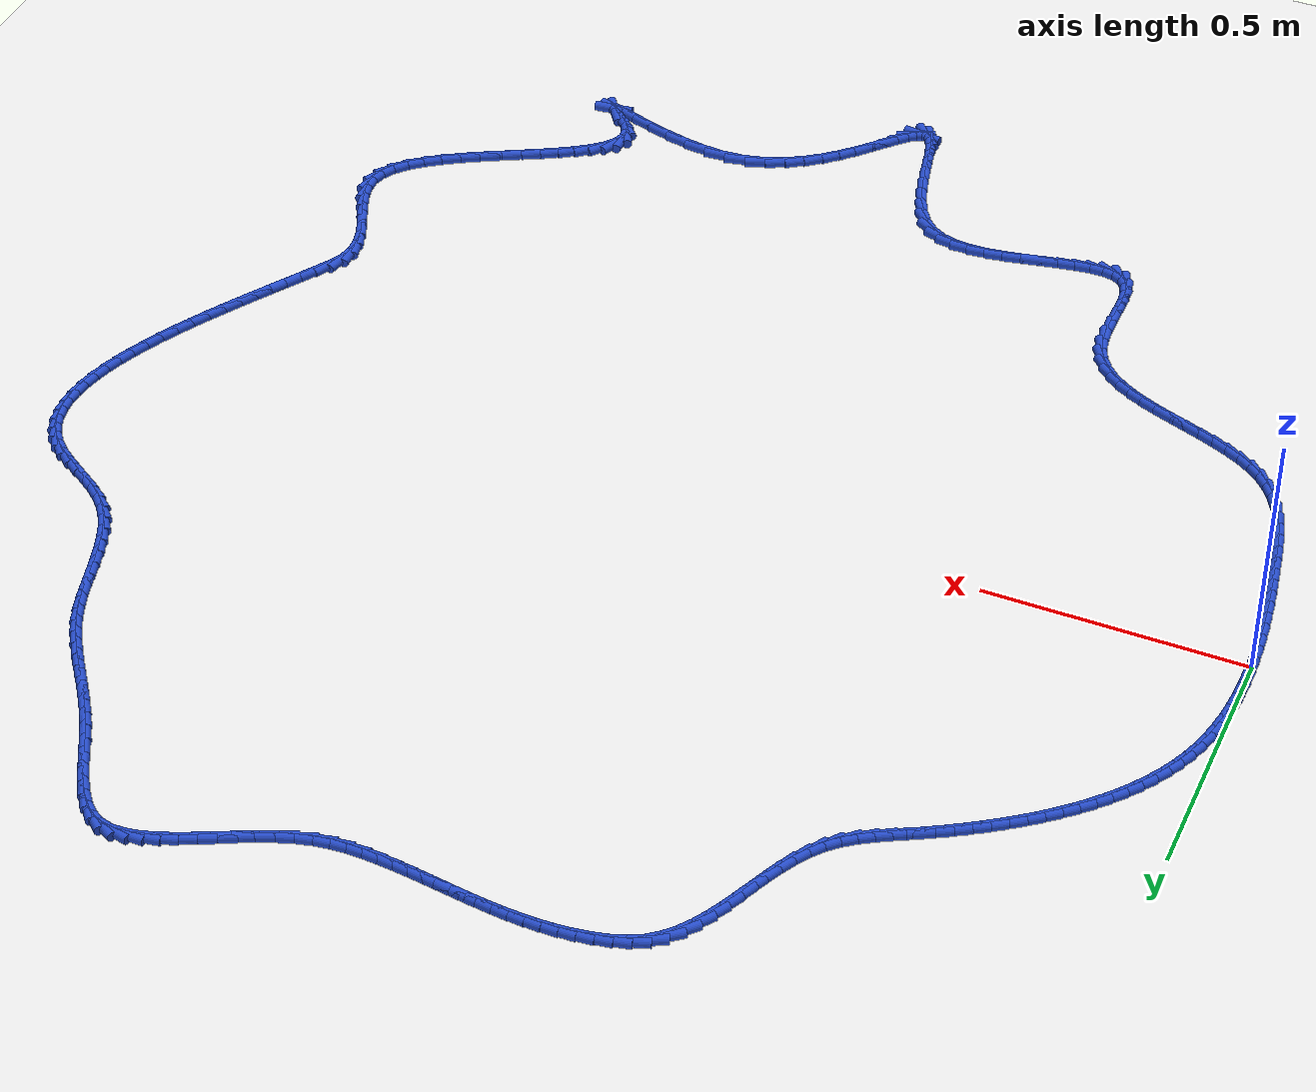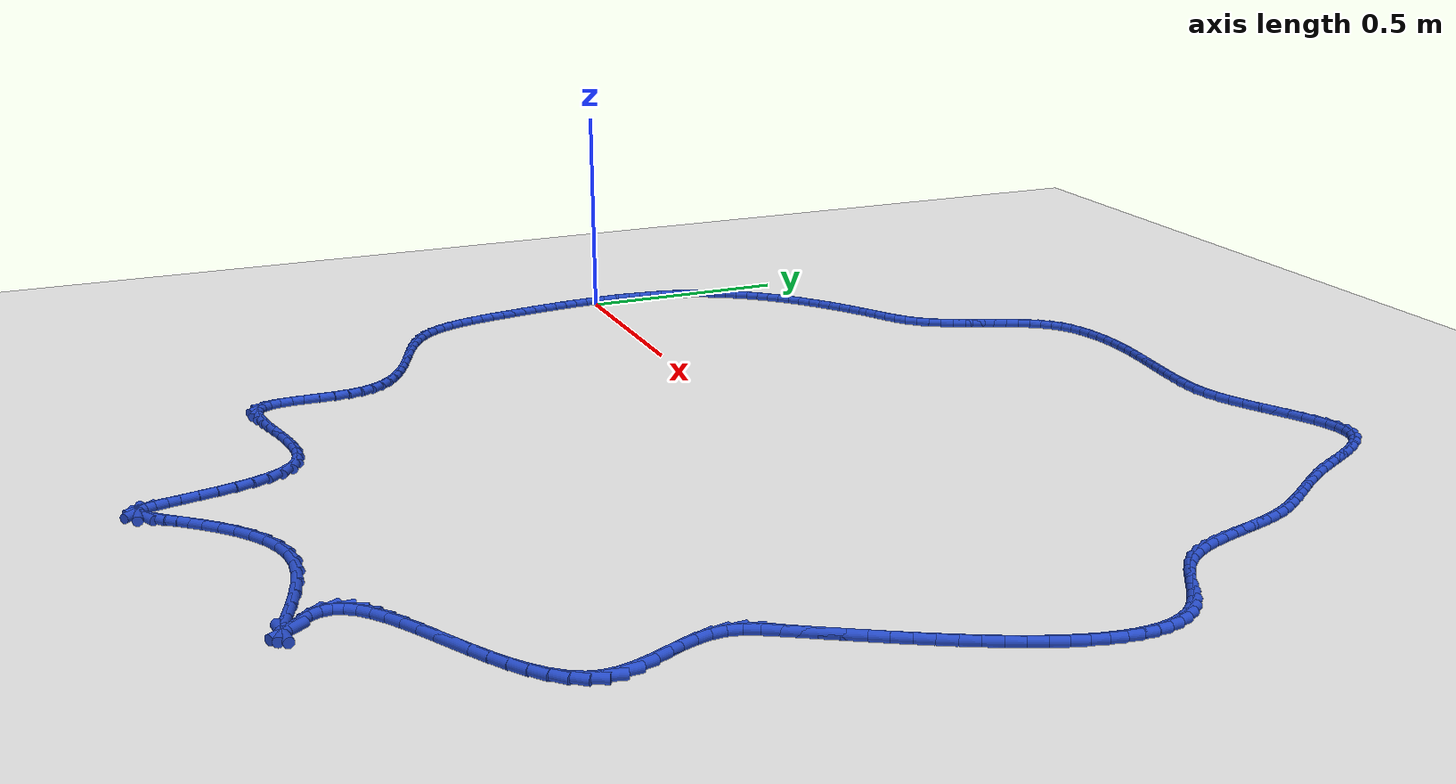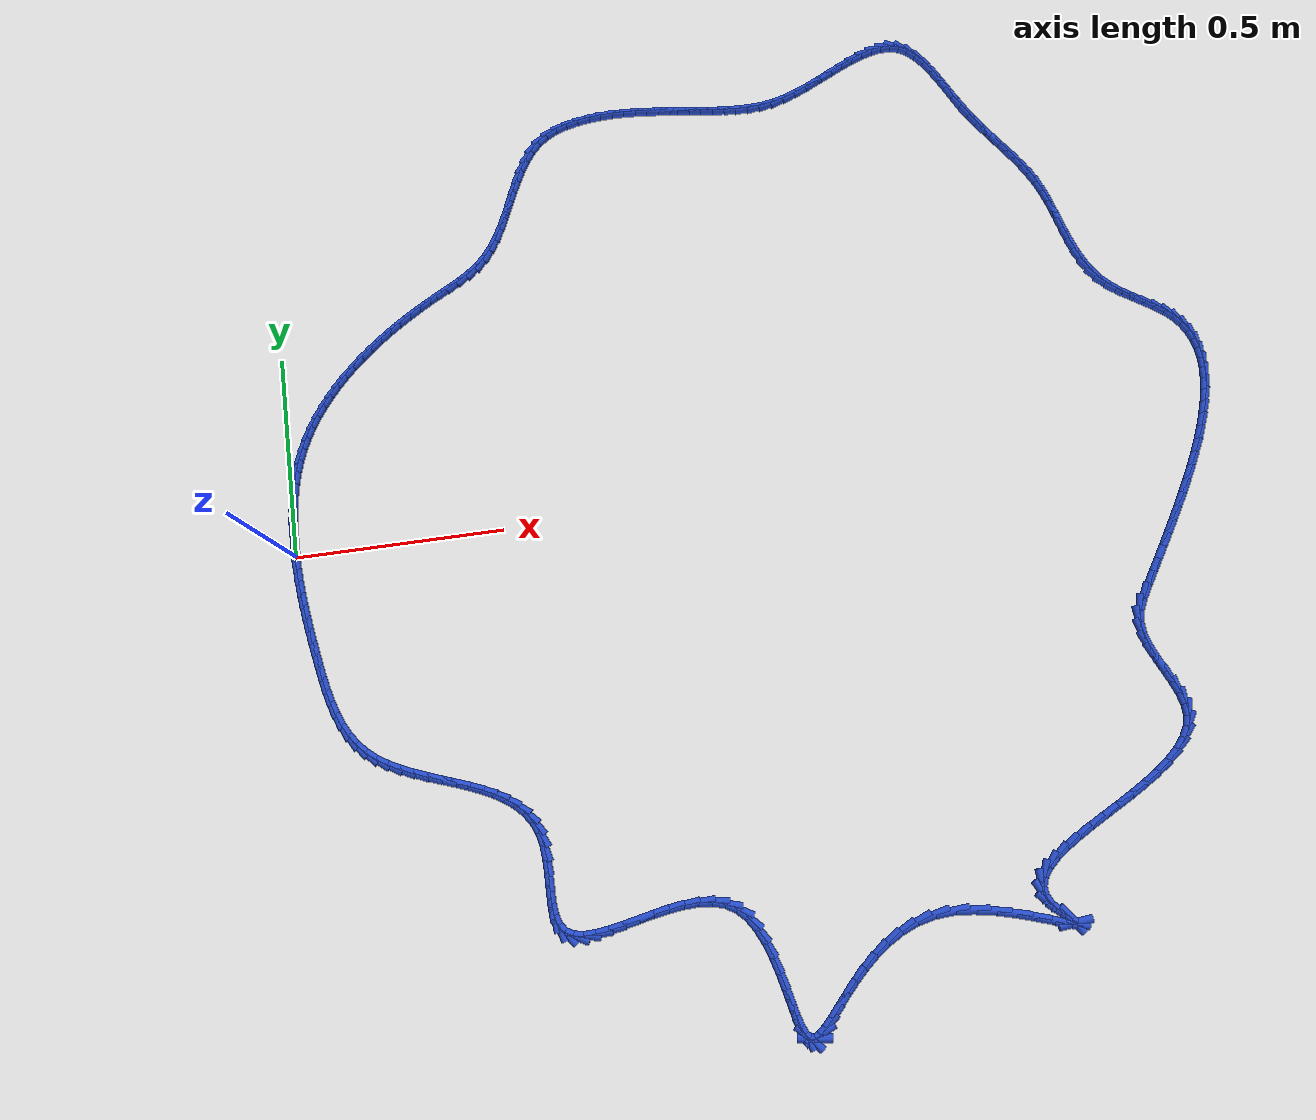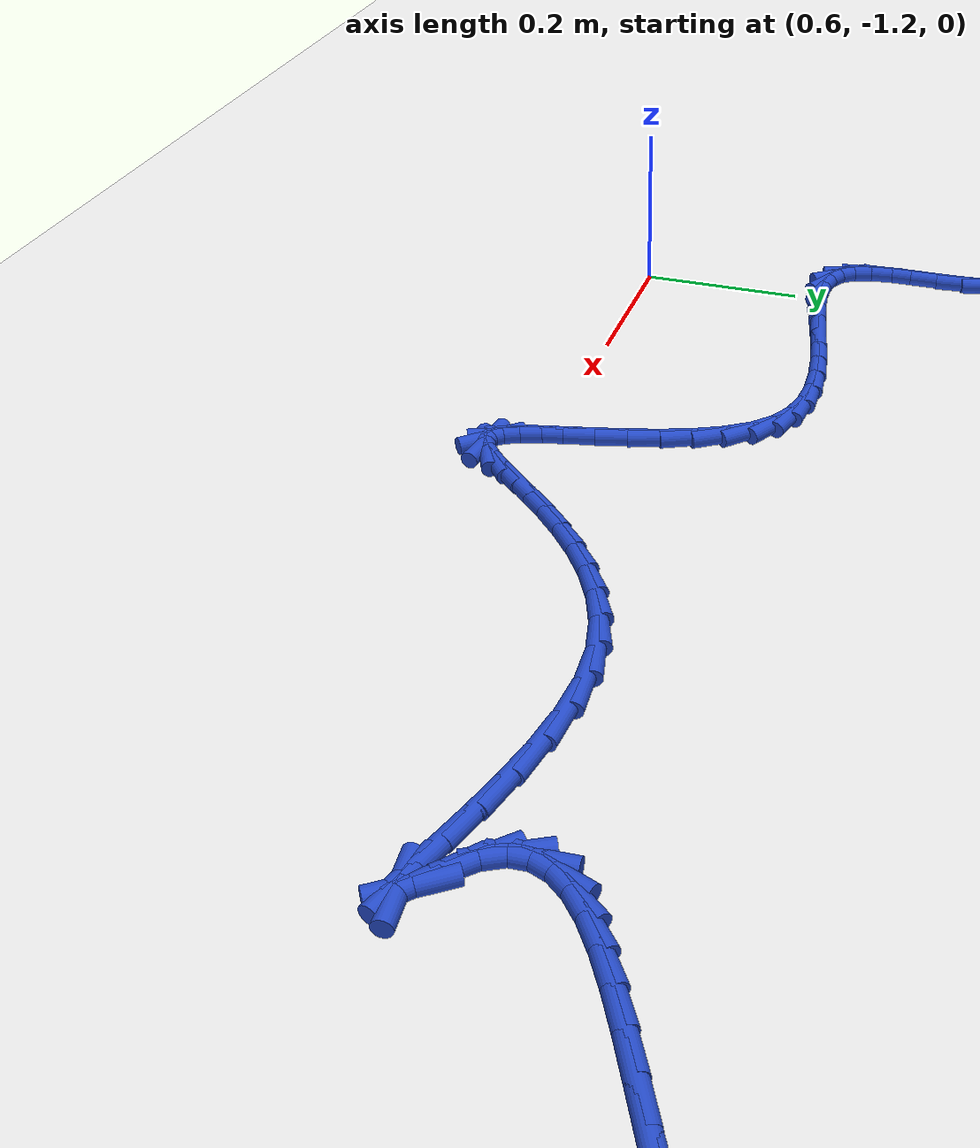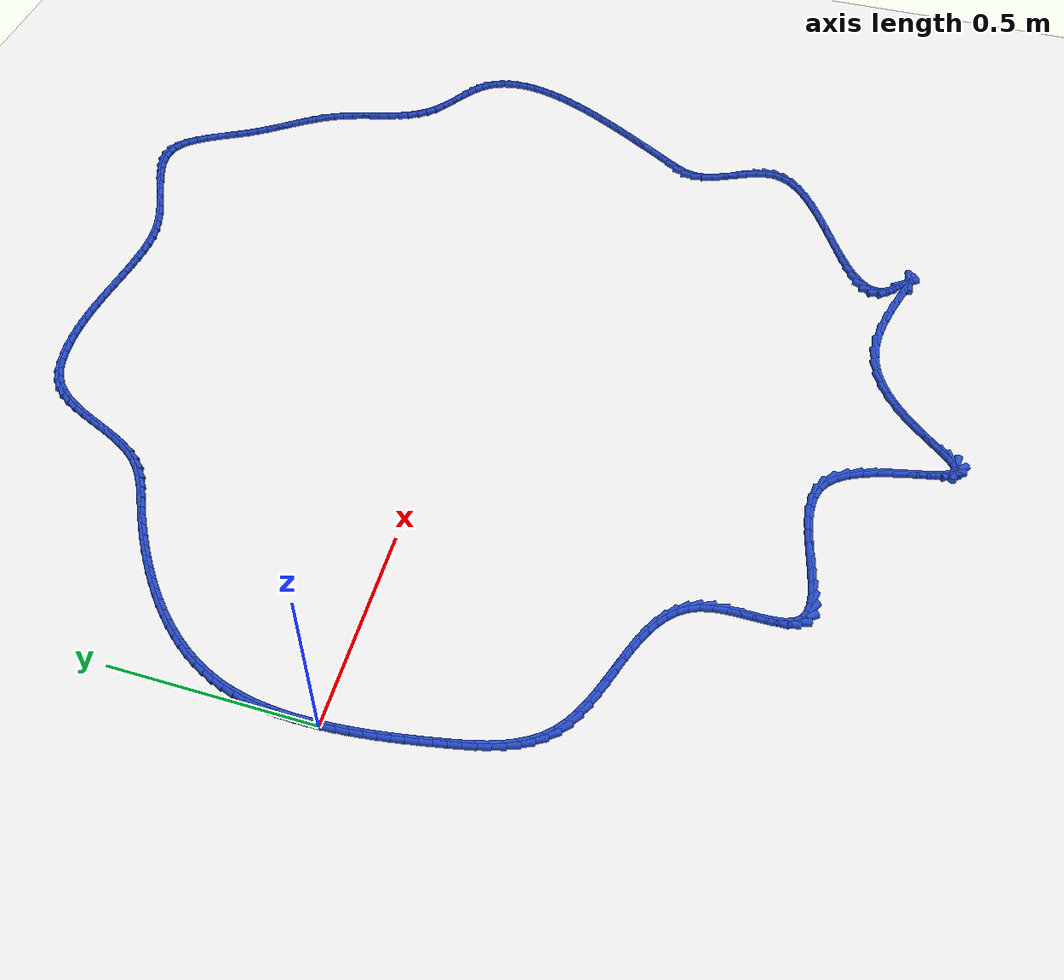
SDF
<sdf version="1.6">
 <world name="default">
  <light name="sun" type="directional">
   <pose>0 0 10 0 -0 0</pose>
   <diffuse>0.8 0.8 0.8 1</diffuse>
   <specular>0.2 0.2 0.2 1</specular>
   <attenuation>
    <range>1000</range>
    <constant>0.9</constant>
    <linear>0.01</linear>
    <quadratic>0.001</quadratic>
   </attenuation>
   <direction>-0.5 0.1 -0.9</direction>
  </light>
  <model name="ground_plane">
   <static>1</static>
   <link name="link">
    <collision name="collision">
     <geometry><plane><normal>0 0 1</normal><size>100 100</size></plane></geometry>
     <surface><friction><ode><mu>100</mu><mu2>50</mu2></ode></friction></surface>
    </collision>
    <visual name="visual">
     <cast_shadows>0</cast_shadows>
     <geometry><plane><normal>0 0 1</normal><size>100 100</size></plane></geometry>
     <material>
      <script><uri>file://media/materials/scripts/gazebo.material</uri><name>Gazebo/WhiteGlow</name></script>
     </material>
    </visual>
   </link>
  </model>
  <gravity>0 0 -9.8</gravity>
  <magnetic_field>6e-06 2.3e-05 -4.2e-05</magnetic_field>
  <atmosphere type="adiabatic"/>
  <physics name="default_physics" default="0" type="ode">
   <max_step_size>0.001</max_step_size>
   <real_time_factor>1</real_time_factor>
   <real_time_update_rate>1000</real_time_update_rate>
  </physics>
  <scene><ambient>0.4 0.4 0.4 1</ambient><background>0.7 0.7 0.7 1</background><shadows>1</shadows></scene>
  <spherical_coordinates>
   <surface_model>EARTH_WGS84</surface_model>
   <latitude_deg>0</latitude_deg>
   <longitude_deg>0</longitude_deg>
   <elevation>0</elevation>
   <heading_deg>0</heading_deg>
  </spherical_coordinates>
  <model name="line">
   <link name="link_0">
    <pose>2.6020852139652106e-18 4.85722573273506e-17 0.01 0 1.57 -1.5473122379264526</pose>
    <collision name="collision">
     <geometry><cylinder><radius>0.01</radius><length>0.08</length></cylinder></geometry>
    </collision>
    <visual name="visual">
     <material>
      <script><name>Gazebo/Blue</name><uri>file://media/materials/scripts/gazebo.material</uri></script>
     </material>
     <geometry><cylinder><radius>0.01</radius><length>0.08</length></cylinder></geometry>
    </visual>
   </link>
   <link name="link_1">
    <pose>-0.0007039272480909441 0.02996913533298461 0.01 0 1.57 1.5633113529502236</pose>
    <collision name="collision">
     <geometry><cylinder><radius>0.01</radius><length>0.08</length></cylinder></geometry>
    </collision>
    <visual name="visual">
     <material>
      <script><name>Gazebo/Blue</name><uri>file://media/materials/scripts/gazebo.material</uri></script>
     </material>
     <geometry><cylinder><radius>0.01</radius><length>0.08</length></cylinder></geometry>
    </visual>
   </link>
   <link name="link_2">
    <pose>-0.0004782376076412418 0.06012093417368127 0.01 0 1.57 1.5284069422193465</pose>
    <collision name="collision">
     <geometry><cylinder><radius>0.01</radius><length>0.08</length></cylinder></geometry>
    </collision>
    <visual name="visual">
     <material>
      <script><name>Gazebo/Blue</name><uri>file://media/materials/scripts/gazebo.material</uri></script>
     </material>
     <geometry><cylinder><radius>0.01</radius><length>0.08</length></cylinder></geometry>
    </visual>
   </link>
   <link name="link_3">
    <pose>0.000802609183513676 0.09031904968383503 0.01 0 1.57 1.4892208433925638</pose>
    <collision name="collision">
     <geometry><cylinder><radius>0.01</radius><length>0.08</length></cylinder></geometry>
    </collision>
    <visual name="visual">
     <material>
      <script><name>Gazebo/Blue</name><uri>file://media/materials/scripts/gazebo.material</uri></script>
     </material>
     <geometry><cylinder><radius>0.01</radius><length>0.08</length></cylinder></geometry>
    </visual>
   </link>
   <link name="link_4">
    <pose>0.00326415338753838 0.12042713502519091 0.01 0 1.57 1.4453683356091211</pose>
    <collision name="collision">
     <geometry><cylinder><radius>0.01</radius><length>0.08</length></cylinder></geometry>
    </collision>
    <visual name="visual">
     <material>
      <script><name>Gazebo/Blue</name><uri>file://media/materials/scripts/gazebo.material</uri></script>
     </material>
     <geometry><cylinder><radius>0.01</radius><length>0.08</length></cylinder></geometry>
    </visual>
   </link>
   <link name="link_5">
    <pose>0.007031935266597433 0.1503088433594939 0.01 0 1.57 1.3964419279009448</pose>
    <collision name="collision">
     <geometry><cylinder><radius>0.01</radius><length>0.08</length></cylinder></geometry>
    </collision>
    <visual name="visual">
     <material>
      <script><name>Gazebo/Blue</name><uri>file://media/materials/scripts/gazebo.material</uri></script>
     </material>
     <geometry><cylinder><radius>0.01</radius><length>0.08</length></cylinder></geometry>
    </visual>
   </link>
   <link name="link_6">
    <pose>0.012231495082855402 0.17982782784848902 0.01 0 1.57 1.3420361859047418</pose>
    <collision name="collision">
     <geometry><cylinder><radius>0.01</radius><length>0.08</length></cylinder></geometry>
    </collision>
    <visual name="visual">
     <material>
      <script><name>Gazebo/Blue</name><uri>file://media/materials/scripts/gazebo.material</uri></script>
     </material>
     <geometry><cylinder><radius>0.01</radius><length>0.08</length></cylinder></geometry>
    </visual>
   </link>
   <link name="link_7">
    <pose>0.018988373098476855 0.20884774165392128 0.01 0 1.57 1.281785231526709</pose>
    <collision name="collision">
     <geometry><cylinder><radius>0.01</radius><length>0.08</length></cylinder></geometry>
    </collision>
    <visual name="visual">
     <material>
      <script><name>Gazebo/Blue</name><uri>file://media/materials/scripts/gazebo.material</uri></script>
     </material>
     <geometry><cylinder><radius>0.01</radius><length>0.08</length></cylinder></geometry>
    </visual>
   </link>
   <link name="link_8">
    <pose>0.027428109575626358 0.23723223793753567 0.01 0 1.57 1.2157204596871165</pose>
    <collision name="collision">
     <geometry><cylinder><radius>0.01</radius><length>0.08</length></cylinder></geometry>
    </collision>
    <visual name="visual">
     <material>
      <script><name>Gazebo/Blue</name><uri>file://media/materials/scripts/gazebo.material</uri></script>
     </material>
     <geometry><cylinder><radius>0.01</radius><length>0.08</length></cylinder></geometry>
    </visual>
   </link>
   <link name="link_9">
    <pose>0.03766852281448814 0.26484995638541303 0.01 0 1.57 1.148590877885111</pose>
    <collision name="collision">
     <geometry><cylinder><radius>0.01</radius><length>0.08</length></cylinder></geometry>
    </collision>
    <visual name="visual">
     <material>
      <script><name>Gazebo/Blue</name><uri>file://media/materials/scripts/gazebo.material</uri></script>
     </material>
     <geometry><cylinder><radius>0.01</radius><length>0.08</length></cylinder></geometry>
    </visual>
   </link>
   <link name="link_10">
    <pose>0.0497065658301504 0.29164758649623557 0.01 0 1.57 1.084515714756067</pose>
    <collision name="collision">
     <geometry><cylinder><radius>0.01</radius><length>0.08</length></cylinder></geometry>
    </collision>
    <visual name="visual">
     <material>
      <script><name>Gazebo/Blue</name><uri>file://media/materials/scripts/gazebo.material</uri></script>
     </material>
     <geometry><cylinder><radius>0.01</radius><length>0.08</length></cylinder></geometry>
    </visual>
   </link>
   <link name="link_11">
    <pose>0.06344335004731635 0.3176337083120544 0.01 0 1.57 1.0238896088188574</pose>
    <collision name="collision">
     <geometry><cylinder><radius>0.01</radius><length>0.08</length></cylinder></geometry>
    </collision>
    <visual name="visual">
     <material>
      <script><name>Gazebo/Blue</name><uri>file://media/materials/scripts/gazebo.material</uri></script>
     </material>
     <geometry><cylinder><radius>0.01</radius><length>0.08</length></cylinder></geometry>
    </visual>
   </link>
   <link name="link_12">
    <pose>0.0787773542475194 0.34281860192722147 0.01 0 1.57 0.9668722112428474</pose>
    <collision name="collision">
     <geometry><cylinder><radius>0.01</radius><length>0.08</length></cylinder></geometry>
    </collision>
    <visual name="visual">
     <material>
      <script><name>Gazebo/Blue</name><uri>file://media/materials/scripts/gazebo.material</uri></script>
     </material>
     <geometry><cylinder><radius>0.01</radius><length>0.08</length></cylinder></geometry>
    </visual>
   </link>
   <link name="link_13">
    <pose>0.09560705721229285 0.36721254743608883 0.01 0 1.57 0.9135110585352482</pose>
    <collision name="collision">
     <geometry><cylinder><radius>0.01</radius><length>0.08</length></cylinder></geometry>
    </collision>
    <visual name="visual">
     <material>
      <script><name>Gazebo/Blue</name><uri>file://media/materials/scripts/gazebo.material</uri></script>
     </material>
     <geometry><cylinder><radius>0.01</radius><length>0.08</length></cylinder></geometry>
    </visual>
   </link>
   <link name="link_14">
    <pose>0.1138309377231701 0.39082582493300844 0.01 0 1.57 0.8637642066965091</pose>
    <collision name="collision">
     <geometry><cylinder><radius>0.01</radius><length>0.08</length></cylinder></geometry>
    </collision>
    <visual name="visual">
     <material>
      <script><name>Gazebo/Blue</name><uri>file://media/materials/scripts/gazebo.material</uri></script>
     </material>
     <geometry><cylinder><radius>0.01</radius><length>0.08</length></cylinder></geometry>
    </visual>
   </link>
   <link name="link_15">
    <pose>0.1333474745616845 0.4136687145123323 0.01 0 1.57 0.8175230093961017</pose>
    <collision name="collision">
     <geometry><cylinder><radius>0.01</radius><length>0.08</length></cylinder></geometry>
    </collision>
    <visual name="visual">
     <material>
      <script><name>Gazebo/Blue</name><uri>file://media/materials/scripts/gazebo.material</uri></script>
     </material>
     <geometry><cylinder><radius>0.01</radius><length>0.08</length></cylinder></geometry>
    </visual>
   </link>
   <link name="link_16">
    <pose>0.15405514650936958 0.43575149626841264 0.01 0 1.57 0.774632772924111</pose>
    <collision name="collision">
     <geometry><cylinder><radius>0.01</radius><length>0.08</length></cylinder></geometry>
    </collision>
    <visual name="visual">
     <material>
      <script><name>Gazebo/Blue</name><uri>file://media/materials/scripts/gazebo.material</uri></script>
     </material>
     <geometry><cylinder><radius>0.01</radius><length>0.08</length></cylinder></geometry>
    </visual>
   </link>
   <link name="link_17">
    <pose>0.1758524323477585 0.4570844502956013 0.01 0 1.57 0.7349101349597975</pose>
    <collision name="collision">
     <geometry><cylinder><radius>0.01</radius><length>0.08</length></cylinder></geometry>
    </collision>
    <visual name="visual">
     <material>
      <script><name>Gazebo/Blue</name><uri>file://media/materials/scripts/gazebo.material</uri></script>
     </material>
     <geometry><cylinder><radius>0.01</radius><length>0.08</length></cylinder></geometry>
    </visual>
   </link>
   <link name="link_18">
    <pose>0.19863781085838475 0.4776778566882504 0.01 0 1.57 0.6981568462999301</pose>
    <collision name="collision">
     <geometry><cylinder><radius>0.01</radius><length>0.08</length></cylinder></geometry>
    </collision>
    <visual name="visual">
     <material>
      <script><name>Gazebo/Blue</name><uri>file://media/materials/scripts/gazebo.material</uri></script>
     </material>
     <geometry><cylinder><radius>0.01</radius><length>0.08</length></cylinder></geometry>
    </visual>
   </link>
   <link name="link_19">
    <pose>0.22230976082278164 0.497541995540712 0.01 0 1.57 0.6641701577719076</pose>
    <collision name="collision">
     <geometry><cylinder><radius>0.01</radius><length>0.08</length></cylinder></geometry>
    </collision>
    <visual name="visual">
     <material>
      <script><name>Gazebo/Blue</name><uri>file://media/materials/scripts/gazebo.material</uri></script>
     </material>
     <geometry><cylinder><radius>0.01</radius><length>0.08</length></cylinder></geometry>
    </visual>
   </link>
   <link name="link_20">
    <pose>0.24676676102248263 0.5166871469473379 0.01 0 1.57 0.6327502825490785</pose>
    <collision name="collision">
     <geometry><cylinder><radius>0.01</radius><length>0.08</length></cylinder></geometry>
    </collision>
    <visual name="visual">
     <material>
      <script><name>Gazebo/Blue</name><uri>file://media/materials/scripts/gazebo.material</uri></script>
     </material>
     <geometry><cylinder><radius>0.01</radius><length>0.08</length></cylinder></geometry>
    </visual>
   </link>
   <link name="link_21">
    <pose>0.27190729023902116 0.5351235910024805 0.01 0 1.57 0.6037054953434049</pose>
    <collision name="collision">
     <geometry><cylinder><radius>0.01</radius><length>0.08</length></cylinder></geometry>
    </collision>
    <visual name="visual">
     <material>
      <script><name>Gazebo/Blue</name><uri>file://media/materials/scripts/gazebo.material</uri></script>
     </material>
     <geometry><cylinder><radius>0.01</radius><length>0.08</length></cylinder></geometry>
    </visual>
   </link>
   <link name="link_22">
    <pose>0.29762982725393033 0.5528616078004915 0.01 0 1.57 0.5768554160180083</pose>
    <collision name="collision">
     <geometry><cylinder><radius>0.01</radius><length>0.08</length></cylinder></geometry>
    </collision>
    <visual name="visual">
     <material>
      <script><name>Gazebo/Blue</name><uri>file://media/materials/scripts/gazebo.material</uri></script>
     </material>
     <geometry><cylinder><radius>0.01</radius><length>0.08</length></cylinder></geometry>
    </visual>
   </link>
   <link name="link_23">
    <pose>0.3238328508487437 0.569911477435723 0.01 0 1.57 0.5520329591945526</pose>
    <collision name="collision">
     <geometry><cylinder><radius>0.01</radius><length>0.08</length></cylinder></geometry>
    </collision>
    <visual name="visual">
     <material>
      <script><name>Gazebo/Blue</name><uri>file://media/materials/scripts/gazebo.material</uri></script>
     </material>
     <geometry><cylinder><radius>0.01</radius><length>0.08</length></cylinder></geometry>
    </visual>
   </link>
   <link name="link_24">
    <pose>0.35041483980499477 0.5862834800025272 0.01 0 1.57 0.529085347737507</pose>
    <collision name="collision">
     <geometry><cylinder><radius>0.01</radius><length>0.08</length></cylinder></geometry>
    </collision>
    <visual name="visual">
     <material>
      <script><name>Gazebo/Blue</name><uri>file://media/materials/scripts/gazebo.material</uri></script>
     </material>
     <geometry><cylinder><radius>0.01</radius><length>0.08</length></cylinder></geometry>
    </visual>
   </link>
   <link name="link_25">
    <pose>0.3772742729042166 0.6019878955952558 0.01 0 1.57 0.5078856126315091</pose>
    <collision name="collision">
     <geometry><cylinder><radius>0.01</radius><length>0.08</length></cylinder></geometry>
    </collision>
    <visual name="visual">
     <material>
      <script><name>Gazebo/Blue</name><uri>file://media/materials/scripts/gazebo.material</uri></script>
     </material>
     <geometry><cylinder><radius>0.01</radius><length>0.08</length></cylinder></geometry>
    </visual>
   </link>
   <link name="link_26">
    <pose>0.4043094402136723 0.6170352925592704 0.01 0 1.57 0.4956130167088213</pose>
    <collision name="collision">
     <geometry><cylinder><radius>0.01</radius><length>0.08</length></cylinder></geometry>
    </collision>
    <visual name="visual">
     <material>
      <script><name>Gazebo/Blue</name><uri>file://media/materials/scripts/gazebo.material</uri></script>
     </material>
     <geometry><cylinder><radius>0.01</radius><length>0.08</length></cylinder></geometry>
    </visual>
   </link>
   <link name="link_27">
    <pose>0.4312954155945691 0.6316244454397921 0.01 0 1.57 0.512548514350395</pose>
    <collision name="collision">
     <geometry><cylinder><radius>0.01</radius><length>0.08</length></cylinder></geometry>
    </collision>
    <visual name="visual">
     <material>
      <script><name>Gazebo/Blue</name><uri>file://media/materials/scripts/gazebo.material</uri></script>
     </material>
     <geometry><cylinder><radius>0.01</radius><length>0.08</length></cylinder></geometry>
    </visual>
   </link>
   <link name="link_28">
    <pose>0.4576717334787862 0.6464666474102233 0.01 0 1.57 0.563572135568817</pose>
    <collision name="collision">
     <geometry><cylinder><radius>0.01</radius><length>0.08</length></cylinder></geometry>
    </collision>
    <visual name="visual">
     <material>
      <script><name>Gazebo/Blue</name><uri>file://media/materials/scripts/gazebo.material</uri></script>
     </material>
     <geometry><cylinder><radius>0.01</radius><length>0.08</length></cylinder></geometry>
    </visual>
   </link>
   <link name="link_29">
    <pose>0.4828213466339723 0.6623596171260314 0.01 0 1.57 0.6506587642174321</pose>
    <collision name="collision">
     <geometry><cylinder><radius>0.01</radius><length>0.08</length></cylinder></geometry>
    </collision>
    <visual name="visual">
     <material>
      <script><name>Gazebo/Blue</name><uri>file://media/materials/scripts/gazebo.material</uri></script>
     </material>
     <geometry><cylinder><radius>0.01</radius><length>0.08</length></cylinder></geometry>
    </visual>
   </link>
   <link name="link_30">
    <pose>0.506127207827776 0.6801010732426844 0.01 0 1.57 0.7736965031014971</pose>
    <collision name="collision">
     <geometry><cylinder><radius>0.01</radius><length>0.08</length></cylinder></geometry>
    </collision>
    <visual name="visual">
     <material>
      <script><name>Gazebo/Blue</name><uri>file://media/materials/scripts/gazebo.material</uri></script>
     </material>
     <geometry><cylinder><radius>0.01</radius><length>0.08</length></cylinder></geometry>
    </visual>
   </link>
   <link name="link_31">
    <pose>0.5269835326541705 0.7004749146477248 0.01 0 1.57 0.9045960670446079</pose>
    <collision name="collision">
     <geometry><cylinder><radius>0.01</radius><length>0.08</length></cylinder></geometry>
    </collision>
    <visual name="visual">
     <material>
      <script><name>Gazebo/Blue</name><uri>file://media/materials/scripts/gazebo.material</uri></script>
     </material>
     <geometry><cylinder><radius>0.01</radius><length>0.08</length></cylinder></geometry>
    </visual>
   </link>
   <link name="link_32">
    <pose>0.5452427222112254 0.7237028352234176 0.01 0 1.57 1.0080555985612134</pose>
    <collision name="collision">
     <geometry><cylinder><radius>0.01</radius><length>0.08</length></cylinder></geometry>
    </collision>
    <visual name="visual">
     <material>
      <script><name>Gazebo/Blue</name><uri>file://media/materials/scripts/gazebo.material</uri></script>
     </material>
     <geometry><cylinder><radius>0.01</radius><length>0.08</length></cylinder></geometry>
    </visual>
   </link>
   <link name="link_33">
    <pose>0.5613644205262538 0.7492614266801145 0.01 0 1.57 1.083181658013889</pose>
    <collision name="collision">
     <geometry><cylinder><radius>0.01</radius><length>0.08</length></cylinder></geometry>
    </collision>
    <visual name="visual">
     <material>
      <script><name>Gazebo/Blue</name><uri>file://media/materials/scripts/gazebo.material</uri></script>
     </material>
     <geometry><cylinder><radius>0.01</radius><length>0.08</length></cylinder></geometry>
    </visual>
   </link>
   <link name="link_34">
    <pose>0.5758500892588475 0.7765759694536607 0.01 0 1.57 1.1326408534506518</pose>
    <collision name="collision">
     <geometry><cylinder><radius>0.01</radius><length>0.08</length></cylinder></geometry>
    </collision>
    <visual name="visual">
     <material>
      <script><name>Gazebo/Blue</name><uri>file://media/materials/scripts/gazebo.material</uri></script>
     </material>
     <geometry><cylinder><radius>0.01</radius><length>0.08</length></cylinder></geometry>
    </visual>
   </link>
   <link name="link_35">
    <pose>0.5892011900685988 0.8050717439799011 0.01 0 1.57 1.158797115858197</pose>
    <collision name="collision">
     <geometry><cylinder><radius>0.01</radius><length>0.08</length></cylinder></geometry>
    </collision>
    <visual name="visual">
     <material>
      <script><name>Gazebo/Blue</name><uri>file://media/materials/scripts/gazebo.material</uri></script>
     </material>
     <geometry><cylinder><radius>0.01</radius><length>0.08</length></cylinder></geometry>
    </visual>
   </link>
   <link name="link_36">
    <pose>0.6019191846150993 0.8341740306946807 0.01 0 1.57 1.1629992175297037</pose>
    <collision name="collision">
     <geometry><cylinder><radius>0.01</radius><length>0.08</length></cylinder></geometry>
    </collision>
    <visual name="visual">
     <material>
      <script><name>Gazebo/Blue</name><uri>file://media/materials/scripts/gazebo.material</uri></script>
     </material>
     <geometry><cylinder><radius>0.01</radius><length>0.08</length></cylinder></geometry>
    </visual>
   </link>
   <link name="link_37">
    <pose>0.614505534557941 0.8633081100338446 0.01 0 1.57 1.1453234444082492</pose>
    <collision name="collision">
     <geometry><cylinder><radius>0.01</radius><length>0.08</length></cylinder></geometry>
    </collision>
    <visual name="visual">
     <material>
      <script><name>Gazebo/Blue</name><uri>file://media/materials/scripts/gazebo.material</uri></script>
     </material>
     <geometry><cylinder><radius>0.01</radius><length>0.08</length></cylinder></geometry>
    </visual>
   </link>
   <link name="link_38">
    <pose>0.627461701556716 0.891899262433238 0.01 0 1.57 1.104511327123926</pose>
    <collision name="collision">
     <geometry><cylinder><radius>0.01</radius><length>0.08</length></cylinder></geometry>
    </collision>
    <visual name="visual">
     <material>
      <script><name>Gazebo/Blue</name><uri>file://media/materials/scripts/gazebo.material</uri></script>
     </material>
     <geometry><cylinder><radius>0.01</radius><length>0.08</length></cylinder></geometry>
    </visual>
   </link>
   <link name="link_39">
    <pose>0.6412891472710159 0.9193727683287055 0.01 0 1.57 1.038069745802098</pose>
    <collision name="collision">
     <geometry><cylinder><radius>0.01</radius><length>0.08</length></cylinder></geometry>
    </collision>
    <visual name="visual">
     <material>
      <script><name>Gazebo/Blue</name><uri>file://media/materials/scripts/gazebo.material</uri></script>
     </material>
     <geometry><cylinder><radius>0.01</radius><length>0.08</length></cylinder></geometry>
    </visual>
   </link>
   <link name="link_40">
    <pose>0.656489333360433 0.9451539081560925 0.01 0 1.57 0.9427442892445876</pose>
    <collision name="collision">
     <geometry><cylinder><radius>0.01</radius><length>0.08</length></cylinder></geometry>
    </collision>
    <visual name="visual">
     <material>
      <script><name>Gazebo/Blue</name><uri>file://media/materials/scripts/gazebo.material</uri></script>
     </material>
     <geometry><cylinder><radius>0.01</radius><length>0.08</length></cylinder></geometry>
    </visual>
   </link>
   <link name="link_41">
    <pose>0.6735637214845588 0.9686679623512437 0.01 0 1.57 0.8158505385536886</pose>
    <collision name="collision">
     <geometry><cylinder><radius>0.01</radius><length>0.08</length></cylinder></geometry>
    </collision>
    <visual name="visual">
     <material>
      <script><name>Gazebo/Blue</name><uri>file://media/materials/scripts/gazebo.material</uri></script>
     </material>
     <geometry><cylinder><radius>0.01</radius><length>0.08</length></cylinder></geometry>
    </visual>
   </link>
   <link name="link_42">
    <pose>0.6930137733029857 0.9893402113500045 0.01 0 1.57 0.6579700808070119</pose>
    <collision name="collision">
     <geometry><cylinder><radius>0.01</radius><length>0.08</length></cylinder></geometry>
    </collision>
    <visual name="visual">
     <material>
      <script><name>Gazebo/Blue</name><uri>file://media/materials/scripts/gazebo.material</uri></script>
     </material>
     <geometry><cylinder><radius>0.01</radius><length>0.08</length></cylinder></geometry>
    </visual>
   </link>
   <link name="link_43">
    <pose>0.7153409504753052 1.0065959355882195 0.01 0 1.57 0.48001958919318843</pose>
    <collision name="collision">
     <geometry><cylinder><radius>0.01</radius><length>0.08</length></cylinder></geometry>
    </collision>
    <visual name="visual">
     <material>
      <script><name>Gazebo/Blue</name><uri>file://media/materials/scripts/gazebo.material</uri></script>
     </material>
     <geometry><cylinder><radius>0.01</radius><length>0.08</length></cylinder></geometry>
    </visual>
   </link>
   <link name="link_44">
    <pose>0.7409533080757175 1.0199306444176994 0.01 0 1.57 0.32969359713967095</pose>
    <collision name="collision">
     <geometry><cylinder><radius>0.01</radius><length>0.08</length></cylinder></geometry>
    </collision>
    <visual name="visual">
     <material>
      <script><name>Gazebo/Blue</name><uri>file://media/materials/scripts/gazebo.material</uri></script>
     </material>
     <geometry><cylinder><radius>0.01</radius><length>0.08</length></cylinder></geometry>
    </visual>
   </link>
   <link name="link_45">
    <pose>0.7692364023389191 1.0296086258023132 0.01 0 1.57 0.2237279969301156</pose>
    <collision name="collision">
     <geometry><cylinder><radius>0.01</radius><length>0.08</length></cylinder></geometry>
    </collision>
    <visual name="visual">
     <material>
      <script><name>Gazebo/Blue</name><uri>file://media/materials/scripts/gazebo.material</uri></script>
     </material>
     <geometry><cylinder><radius>0.01</radius><length>0.08</length></cylinder></geometry>
    </visual>
   </link>
   <link name="link_46">
    <pose>0.7989450000686684 1.0363684346727768 0.01 0 1.57 0.15007415062330498</pose>
    <collision name="collision">
     <geometry><cylinder><radius>0.01</radius><length>0.08</length></cylinder></geometry>
    </collision>
    <visual name="visual">
     <material>
      <script><name>Gazebo/Blue</name><uri>file://media/materials/scripts/gazebo.material</uri></script>
     </material>
     <geometry><cylinder><radius>0.01</radius><length>0.08</length></cylinder></geometry>
    </visual>
   </link>
   <link name="link_47">
    <pose>0.8289473169587279 1.0409051169102694 0.01 0 1.57 0.0891030732480868</pose>
    <collision name="collision">
     <geometry><cylinder><radius>0.01</radius><length>0.08</length></cylinder></geometry>
    </collision>
    <visual name="visual">
     <material>
      <script><name>Gazebo/Blue</name><uri>file://media/materials/scripts/gazebo.material</uri></script>
     </material>
     <geometry><cylinder><radius>0.01</radius><length>0.08</length></cylinder></geometry>
    </visual>
   </link>
   <link name="link_48">
    <pose>0.8589165535003263 1.0435825574616524 0.01 0 1.57 0.03501761102344548</pose>
    <collision name="collision">
     <geometry><cylinder><radius>0.01</radius><length>0.08</length></cylinder></geometry>
    </collision>
    <visual name="visual">
     <material>
      <script><name>Gazebo/Blue</name><uri>file://media/materials/scripts/gazebo.material</uri></script>
     </material>
     <geometry><cylinder><radius>0.01</radius><length>0.08</length></cylinder></geometry>
    </visual>
   </link>
   <link name="link_49">
    <pose>0.888850292932611 1.0446311941649518 0.01 0 1.57 -0.011709678779971793</pose>
    <collision name="collision">
     <geometry><cylinder><radius>0.01</radius><length>0.08</length></cylinder></geometry>
    </collision>
    <visual name="visual">
     <material>
      <script><name>Gazebo/Blue</name><uri>file://media/materials/scripts/gazebo.material</uri></script>
     </material>
     <geometry><cylinder><radius>0.01</radius><length>0.08</length></cylinder></geometry>
    </visual>
   </link>
   <link name="link_50">
    <pose>0.9187470122362672 1.0442810971838181 0.01 0 1.57 -0.050822015321530814</pose>
    <collision name="collision">
     <geometry><cylinder><radius>0.01</radius><length>0.08</length></cylinder></geometry>
    </collision>
    <visual name="visual">
     <material>
      <script><name>Gazebo/Blue</name><uri>file://media/materials/scripts/gazebo.material</uri></script>
     </material>
     <geometry><cylinder><radius>0.01</radius><length>0.08</length></cylinder></geometry>
    </visual>
   </link>
   <link name="link_51">
    <pose>0.9486051883919803 1.0427623366819025 0.01 0 1.57 -0.08222564272332829</pose>
    <collision name="collision">
     <geometry><cylinder><radius>0.01</radius><length>0.08</length></cylinder></geometry>
    </collision>
    <visual name="visual">
     <material>
      <script><name>Gazebo/Blue</name><uri>file://media/materials/scripts/gazebo.material</uri></script>
     </material>
     <geometry><cylinder><radius>0.01</radius><length>0.08</length></cylinder></geometry>
    </visual>
   </link>
   <link name="link_52">
    <pose>0.978423298380436 1.040304982822856 0.01 0 1.57 -0.10592332431333239</pose>
    <collision name="collision">
     <geometry><cylinder><radius>0.01</radius><length>0.08</length></cylinder></geometry>
    </collision>
    <visual name="visual">
     <material>
      <script><name>Gazebo/Blue</name><uri>file://media/materials/scripts/gazebo.material</uri></script>
     </material>
     <geometry><cylinder><radius>0.01</radius><length>0.08</length></cylinder></geometry>
    </visual>
   </link>
   <link name="link_53">
    <pose>1.008199819182319 1.037139105770329 0.01 0 1.57 -0.12195855962618113</pose>
    <collision name="collision">
     <geometry><cylinder><radius>0.01</radius><length>0.08</length></cylinder></geometry>
    </collision>
    <visual name="visual">
     <material>
      <script><name>Gazebo/Blue</name><uri>file://media/materials/scripts/gazebo.material</uri></script>
     </material>
     <geometry><cylinder><radius>0.01</radius><length>0.08</length></cylinder></geometry>
    </visual>
   </link>
   <link name="link_54">
    <pose>1.0379332277783155 1.0334947756879727 0.01 0 1.57 -0.13037361600656563</pose>
    <collision name="collision">
     <geometry><cylinder><radius>0.01</radius><length>0.08</length></cylinder></geometry>
    </collision>
    <visual name="visual">
     <material>
      <script><name>Gazebo/Blue</name><uri>file://media/materials/scripts/gazebo.material</uri></script>
     </material>
     <geometry><cylinder><radius>0.01</radius><length>0.08</length></cylinder></geometry>
    </visual>
   </link>
   <link name="link_55">
    <pose>1.0676220011491104 1.029602062739438 0.01 0 1.57 -0.13118159164379417</pose>
    <collision name="collision">
     <geometry><cylinder><radius>0.01</radius><length>0.08</length></cylinder></geometry>
    </collision>
    <visual name="visual">
     <material>
      <script><name>Gazebo/Blue</name><uri>file://media/materials/scripts/gazebo.material</uri></script>
     </material>
     <geometry><cylinder><radius>0.01</radius><length>0.08</length></cylinder></geometry>
    </visual>
   </link>
   <link name="link_56">
    <pose>1.0972646162753887 1.0256910370883754 0.01 0 1.57 -0.1243517160511117</pose>
    <collision name="collision">
     <geometry><cylinder><radius>0.01</radius><length>0.08</length></cylinder></geometry>
    </collision>
    <visual name="visual">
     <material>
      <script><name>Gazebo/Blue</name><uri>file://media/materials/scripts/gazebo.material</uri></script>
     </material>
     <geometry><cylinder><radius>0.01</radius><length>0.08</length></cylinder></geometry>
    </visual>
   </link>
   <link name="link_57">
    <pose>1.1268595501378365 1.0219917688984357 0.01 0 1.57 -0.10980732972290626</pose>
    <collision name="collision">
     <geometry><cylinder><radius>0.01</radius><length>0.08</length></cylinder></geometry>
    </collision>
    <visual name="visual">
     <material>
      <script><name>Gazebo/Blue</name><uri>file://media/materials/scripts/gazebo.material</uri></script>
     </material>
     <geometry><cylinder><radius>0.01</radius><length>0.08</length></cylinder></geometry>
    </visual>
   </link>
   <link name="link_58">
    <pose>1.156405279717139 1.0187343283332702 0.01 0 1.57 -0.08743686101702561</pose>
    <collision name="collision">
     <geometry><cylinder><radius>0.01</radius><length>0.08</length></cylinder></geometry>
    </collision>
    <visual name="visual">
     <material>
      <script><name>Gazebo/Blue</name><uri>file://media/materials/scripts/gazebo.material</uri></script>
     </material>
     <geometry><cylinder><radius>0.01</radius><length>0.08</length></cylinder></geometry>
    </visual>
   </link>
   <link name="link_59">
    <pose>1.185900281993981 1.0161487855565294 0.01 0 1.57 -0.05635765165588818</pose>
    <collision name="collision">
     <geometry><cylinder><radius>0.01</radius><length>0.08</length></cylinder></geometry>
    </collision>
    <visual name="visual">
     <material>
      <script><name>Gazebo/Blue</name><uri>file://media/materials/scripts/gazebo.material</uri></script>
     </material>
     <geometry><cylinder><radius>0.01</radius><length>0.08</length></cylinder></geometry>
    </visual>
   </link>
   <link name="link_60">
    <pose>1.215351064227917 1.0144872491421746 0.01 0 1.57 -0.008259198600788196</pose>
    <collision name="collision">
     <geometry><cylinder><radius>0.01</radius><length>0.08</length></cylinder></geometry>
    </collision>
    <visual name="visual">
     <material>
      <script><name>Gazebo/Blue</name><uri>file://media/materials/scripts/gazebo.material</uri></script>
     </material>
     <geometry><cylinder><radius>0.01</radius><length>0.08</length></cylinder></geometry>
    </visual>
   </link>
   <link name="link_61">
    <pose>1.2448522253377379 1.0142435876531852 0.01 0 1.57 0.0611166905343832</pose>
    <collision name="collision">
     <geometry><cylinder><radius>0.01</radius><length>0.08</length></cylinder></geometry>
    </collision>
    <visual name="visual">
     <material>
      <script><name>Gazebo/Blue</name><uri>file://media/materials/scripts/gazebo.material</uri></script>
     </material>
     <geometry><cylinder><radius>0.01</radius><length>0.08</length></cylinder></geometry>
    </visual>
   </link>
   <link name="link_62">
    <pose>1.2745527955387879 1.0160610516686273 0.01 0 1.57 0.14942943219591917</pose>
    <collision name="collision">
     <geometry><cylinder><radius>0.01</radius><length>0.08</length></cylinder></geometry>
    </collision>
    <visual name="visual">
     <material>
      <script><name>Gazebo/Blue</name><uri>file://media/materials/scripts/gazebo.material</uri></script>
     </material>
     <geometry><cylinder><radius>0.01</radius><length>0.08</length></cylinder></geometry>
    </visual>
   </link>
   <link name="link_63">
    <pose>1.3046026101757537 1.0205851013758647 0.01 0 1.57 0.25008186617776634</pose>
    <collision name="collision">
     <geometry><cylinder><radius>0.01</radius><length>0.08</length></cylinder></geometry>
    </collision>
    <visual name="visual">
     <material>
      <script><name>Gazebo/Blue</name><uri>file://media/materials/scripts/gazebo.material</uri></script>
     </material>
     <geometry><cylinder><radius>0.01</radius><length>0.08</length></cylinder></geometry>
    </visual>
   </link>
   <link name="link_64">
    <pose>1.3351321515746652 1.0283832354786882 0.01 0 1.57 0.33535875574656215</pose>
    <collision name="collision">
     <geometry><cylinder><radius>0.01</radius><length>0.08</length></cylinder></geometry>
    </collision>
    <visual name="visual">
     <material>
      <script><name>Gazebo/Blue</name><uri>file://media/materials/scripts/gazebo.material</uri></script>
     </material>
     <geometry><cylinder><radius>0.01</radius><length>0.08</length></cylinder></geometry>
    </visual>
   </link>
   <link name="link_65">
    <pose>1.3660580938190656 1.0391616499519527 0.01 0 1.57 0.3939400495281755</pose>
    <collision name="collision">
     <geometry><cylinder><radius>0.01</radius><length>0.08</length></cylinder></geometry>
    </collision>
    <visual name="visual">
     <material>
      <script><name>Gazebo/Blue</name><uri>file://media/materials/scripts/gazebo.material</uri></script>
     </material>
     <geometry><cylinder><radius>0.01</radius><length>0.08</length></cylinder></geometry>
    </visual>
   </link>
   <link name="link_66">
    <pose>1.397164295591988 1.0520915086988987 0.01 0 1.57 0.4298895183108862</pose>
    <collision name="collision">
     <geometry><cylinder><radius>0.01</radius><length>0.08</length></cylinder></geometry>
    </collision>
    <visual name="visual">
     <material>
      <script><name>Gazebo/Blue</name><uri>file://media/materials/scripts/gazebo.material</uri></script>
     </material>
     <geometry><cylinder><radius>0.01</radius><length>0.08</length></cylinder></geometry>
    </visual>
   </link>
   <link name="link_67">
    <pose>1.4282326212708085 1.0663359417841962 0.01 0 1.57 0.44573077141376255</pose>
    <collision name="collision">
     <geometry><cylinder><radius>0.01</radius><length>0.08</length></cylinder></geometry>
    </collision>
    <visual name="visual">
     <material>
      <script><name>Gazebo/Blue</name><uri>file://media/materials/scripts/gazebo.material</uri></script>
     </material>
     <geometry><cylinder><radius>0.01</radius><length>0.08</length></cylinder></geometry>
    </visual>
   </link>
   <link name="link_68">
    <pose>1.4590449352329022 1.081058079272515 0.01 0 1.57 0.44216587081122244</pose>
    <collision name="collision">
     <geometry><cylinder><radius>0.01</radius><length>0.08</length></cylinder></geometry>
    </collision>
    <visual name="visual">
     <material>
      <script><name>Gazebo/Blue</name><uri>file://media/materials/scripts/gazebo.material</uri></script>
     </material>
     <geometry><cylinder><radius>0.01</radius><length>0.08</length></cylinder></geometry>
    </visual>
   </link>
   <link name="link_69">
    <pose>1.489383101855645 1.0954210512285256 0.01 0 1.57 0.4179704605778861</pose>
    <collision name="collision">
     <geometry><cylinder><radius>0.01</radius><length>0.08</length></cylinder></geometry>
    </collision>
    <visual name="visual">
     <material>
      <script><name>Gazebo/Blue</name><uri>file://media/materials/scripts/gazebo.material</uri></script>
     </material>
     <geometry><cylinder><radius>0.01</radius><length>0.08</length></cylinder></geometry>
    </visual>
   </link>
   <link name="link_70">
    <pose>1.5190289855164125 1.1085879877168978 0.01 0 1.57 0.36965519244252804</pose>
    <collision name="collision">
     <geometry><cylinder><radius>0.01</radius><length>0.08</length></cylinder></geometry>
    </collision>
    <visual name="visual">
     <material>
      <script><name>Gazebo/Blue</name><uri>file://media/materials/scripts/gazebo.material</uri></script>
     </material>
     <geometry><cylinder><radius>0.01</radius><length>0.08</length></cylinder></geometry>
    </visual>
   </link>
   <link name="link_71">
    <pose>1.5477644505925805 1.1197220188023014 0.01 0 1.57 0.29086457881611877</pose>
    <collision name="collision">
     <geometry><cylinder><radius>0.01</radius><length>0.08</length></cylinder></geometry>
    </collision>
    <visual name="visual">
     <material>
      <script><name>Gazebo/Blue</name><uri>file://media/materials/scripts/gazebo.material</uri></script>
     </material>
     <geometry><cylinder><radius>0.01</radius><length>0.08</length></cylinder></geometry>
    </visual>
   </link>
   <link name="link_72">
    <pose>1.5753713614615246 1.1279862745494067 0.01 0 1.57 0.17184391983965852</pose>
    <collision name="collision">
     <geometry><cylinder><radius>0.01</radius><length>0.08</length></cylinder></geometry>
    </collision>
    <visual name="visual">
     <material>
      <script><name>Gazebo/Blue</name><uri>file://media/materials/scripts/gazebo.material</uri></script>
     </material>
     <geometry><cylinder><radius>0.01</radius><length>0.08</length></cylinder></geometry>
    </visual>
   </link>
   <link name="link_73">
    <pose>1.60163158250062 1.1325438850228837 0.01 0 1.57 0.0005707648188440943</pose>
    <collision name="collision">
     <geometry><cylinder><radius>0.01</radius><length>0.08</length></cylinder></geometry>
    </collision>
    <visual name="visual">
     <material>
      <script><name>Gazebo/Blue</name><uri>file://media/materials/scripts/gazebo.material</uri></script>
     </material>
     <geometry><cylinder><radius>0.01</radius><length>0.08</length></cylinder></geometry>
    </visual>
   </link>
   <link name="link_74">
    <pose>1.626326978087243 1.1325579802874026 0.01 0 1.57 -0.23006187383835505</pose>
    <collision name="collision">
     <geometry><cylinder><radius>0.01</radius><length>0.08</length></cylinder></geometry>
    </collision>
    <visual name="visual">
     <material>
      <script><name>Gazebo/Blue</name><uri>file://media/materials/scripts/gazebo.material</uri></script>
     </material>
     <geometry><cylinder><radius>0.01</radius><length>0.08</length></cylinder></geometry>
    </visual>
   </link>
   <link name="link_75">
    <pose>1.6492394125987686 1.1271916904076331 0.01 0 1.57 -0.4998905959864863</pose>
    <collision name="collision">
     <geometry><cylinder><radius>0.01</radius><length>0.08</length></cylinder></geometry>
    </collision>
    <visual name="visual">
     <material>
      <script><name>Gazebo/Blue</name><uri>file://media/materials/scripts/gazebo.material</uri></script>
     </material>
     <geometry><cylinder><radius>0.01</radius><length>0.08</length></cylinder></geometry>
    </visual>
   </link>
   <link name="link_76">
    <pose>1.670193851416984 1.1157472048180916 0.01 0 1.57 -0.7271024810349903</pose>
    <collision name="collision">
     <geometry><cylinder><radius>0.01</radius><length>0.08</length></cylinder></geometry>
    </collision>
    <visual name="visual">
     <material>
      <script><name>Gazebo/Blue</name><uri>file://media/materials/scripts/gazebo.material</uri></script>
     </material>
     <geometry><cylinder><radius>0.01</radius><length>0.08</length></cylinder></geometry>
    </visual>
   </link>
   <link name="link_77">
    <pose>1.6893735726147119 1.098682758797335 0.01 0 1.57 -0.8836952000375713</pose>
    <collision name="collision">
     <geometry><cylinder><radius>0.01</radius><length>0.08</length></cylinder></geometry>
    </collision>
    <visual name="visual">
     <material>
      <script><name>Gazebo/Blue</name><uri>file://media/materials/scripts/gazebo.material</uri></script>
     </material>
     <geometry><cylinder><radius>0.01</radius><length>0.08</length></cylinder></geometry>
    </visual>
   </link>
   <link name="link_78">
    <pose>1.7071394502286417 1.0770295761925144 0.01 0 1.57 -0.98527541732175</pose>
    <collision name="collision">
     <geometry><cylinder><radius>0.01</radius><length>0.08</length></cylinder></geometry>
    </collision>
    <visual name="visual">
     <material>
      <script><name>Gazebo/Blue</name><uri>file://media/materials/scripts/gazebo.material</uri></script>
     </material>
     <geometry><cylinder><radius>0.01</radius><length>0.08</length></cylinder></geometry>
    </visual>
   </link>
   <link name="link_79">
    <pose>1.7238536321990623 1.0518229909227907 0.01 0 1.57 -1.0467162234346208</pose>
    <collision name="collision">
     <geometry><cylinder><radius>0.01</radius><length>0.08</length></cylinder></geometry>
    </collision>
    <visual name="visual">
     <material>
      <script><name>Gazebo/Blue</name><uri>file://media/materials/scripts/gazebo.material</uri></script>
     </material>
     <geometry><cylinder><radius>0.01</radius><length>0.08</length></cylinder></geometry>
    </visual>
   </link>
   <link name="link_80">
    <pose>1.7398782664662635 1.0240983369073253 0.01 0 1.57 -1.0776468118597726</pose>
    <collision name="collision">
     <geometry><cylinder><radius>0.01</radius><length>0.08</length></cylinder></geometry>
    </collision>
    <visual name="visual">
     <material>
      <script><name>Gazebo/Blue</name><uri>file://media/materials/scripts/gazebo.material</uri></script>
     </material>
     <geometry><cylinder><radius>0.01</radius><length>0.08</length></cylinder></geometry>
    </visual>
   </link>
   <link name="link_81">
    <pose>1.7555755009705327 0.9948909480652782 0.01 0 1.57 -1.0830444059983302</pose>
    <collision name="collision">
     <geometry><cylinder><radius>0.01</radius><length>0.08</length></cylinder></geometry>
    </collision>
    <visual name="visual">
     <material>
      <script><name>Gazebo/Blue</name><uri>file://media/materials/scripts/gazebo.material</uri></script>
     </material>
     <geometry><cylinder><radius>0.01</radius><length>0.08</length></cylinder></geometry>
    </visual>
   </link>
   <link name="link_82">
    <pose>1.77130748365216 0.965236158315811 0.01 0 1.57 -1.064207322664841</pose>
    <collision name="collision">
     <geometry><cylinder><radius>0.01</radius><length>0.08</length></cylinder></geometry>
    </collision>
    <visual name="visual">
     <material>
      <script><name>Gazebo/Blue</name><uri>file://media/materials/scripts/gazebo.material</uri></script>
     </material>
     <geometry><cylinder><radius>0.01</radius><length>0.08</length></cylinder></geometry>
    </visual>
   </link>
   <link name="link_83">
    <pose>1.7874363624514342 0.9361693015780844 0.01 0 1.57 -1.023710059965437</pose>
    <collision name="collision">
     <geometry><cylinder><radius>0.01</radius><length>0.08</length></cylinder></geometry>
    </collision>
    <visual name="visual">
     <material>
      <script><name>Gazebo/Blue</name><uri>file://media/materials/scripts/gazebo.material</uri></script>
     </material>
     <geometry><cylinder><radius>0.01</radius><length>0.08</length></cylinder></geometry>
    </visual>
   </link>
   <link name="link_84">
    <pose>1.804249563611364 0.9085661023460609 0.01 0 1.57 -0.984880510793661</pose>
    <collision name="collision">
     <geometry><cylinder><radius>0.01</radius><length>0.08</length></cylinder></geometry>
    </collision>
    <visual name="visual">
     <material>
      <script><name>Gazebo/Blue</name><uri>file://media/materials/scripts/gazebo.material</uri></script>
     </material>
     <geometry><cylinder><radius>0.01</radius><length>0.08</length></cylinder></geometry>
    </visual>
   </link>
   <link name="link_85">
    <pose>1.8216132490646366 0.8824024426733574 0.01 0 1.57 -0.9577037035107082</pose>
    <collision name="collision">
     <geometry><cylinder><radius>0.01</radius><length>0.08</length></cylinder></geometry>
    </collision>
    <visual name="visual">
     <material>
      <script><name>Gazebo/Blue</name><uri>file://media/materials/scripts/gazebo.material</uri></script>
     </material>
     <geometry><cylinder><radius>0.01</radius><length>0.08</length></cylinder></geometry>
    </visual>
   </link>
   <link name="link_86">
    <pose>1.8392460849113683 0.8573391458567308 0.01 0 1.57 -0.9434551822479464</pose>
    <collision name="collision">
     <geometry><cylinder><radius>0.01</radius><length>0.08</length></cylinder></geometry>
    </collision>
    <visual name="visual">
     <material>
      <script><name>Gazebo/Blue</name><uri>file://media/materials/scripts/gazebo.material</uri></script>
     </material>
     <geometry><cylinder><radius>0.01</radius><length>0.08</length></cylinder></geometry>
    </visual>
   </link>
   <link name="link_87">
    <pose>1.8568665801765267 0.8330366996722612 0.01 0 1.57 -0.9431352384406895</pose>
    <collision name="collision">
     <geometry><cylinder><radius>0.01</radius><length>0.08</length></cylinder></geometry>
    </collision>
    <visual name="visual">
     <material>
      <script><name>Gazebo/Blue</name><uri>file://media/materials/scripts/gazebo.material</uri></script>
     </material>
     <geometry><cylinder><radius>0.01</radius><length>0.08</length></cylinder></geometry>
    </visual>
   </link>
   <link name="link_88">
    <pose>1.8741932438850775 0.8091555918960279 0.01 0 1.57 -0.9574850481734419</pose>
    <collision name="collision">
     <geometry><cylinder><radius>0.01</radius><length>0.08</length></cylinder></geometry>
    </collision>
    <visual name="visual">
     <material>
      <script><name>Gazebo/Blue</name><uri>file://media/materials/scripts/gazebo.material</uri></script>
     </material>
     <geometry><cylinder><radius>0.01</radius><length>0.08</length></cylinder></geometry>
    </visual>
   </link>
   <link name="link_89">
    <pose>1.8909445850619886 0.78535631030411 0.01 0 1.57 -0.9869332958429147</pose>
    <collision name="collision">
     <geometry><cylinder><radius>0.01</radius><length>0.08</length></cylinder></geometry>
    </collision>
    <visual name="visual">
     <material>
      <script><name>Gazebo/Blue</name><uri>file://media/materials/scripts/gazebo.material</uri></script>
     </material>
     <geometry><cylinder><radius>0.01</radius><length>0.08</length></cylinder></geometry>
    </visual>
   </link>
   <link name="link_90">
    <pose>1.9068391127322266 0.7612993426725871 0.01 0 1.57 -1.0314594468775058</pose>
    <collision name="collision">
     <geometry><cylinder><radius>0.01</radius><length>0.08</length></cylinder></geometry>
    </collision>
    <visual name="visual">
     <material>
      <script><name>Gazebo/Blue</name><uri>file://media/materials/scripts/gazebo.material</uri></script>
     </material>
     <geometry><cylinder><radius>0.01</radius><length>0.08</length></cylinder></geometry>
    </visual>
   </link>
   <link name="link_91">
    <pose>1.9215953359207578 0.7366451767775387 0.01 0 1.57 -1.0903801471559447</pose>
    <collision name="collision">
     <geometry><cylinder><radius>0.01</radius><length>0.08</length></cylinder></geometry>
    </collision>
    <visual name="visual">
     <material>
      <script><name>Gazebo/Blue</name><uri>file://media/materials/scripts/gazebo.material</uri></script>
     </material>
     <geometry><cylinder><radius>0.01</radius><length>0.08</length></cylinder></geometry>
    </visual>
   </link>
   <link name="link_92">
    <pose>1.934931763652549 0.7110543003950445 0.01 0 1.57 -1.161731686605096</pose>
    <collision name="collision">
     <geometry><cylinder><radius>0.01</radius><length>0.08</length></cylinder></geometry>
    </collision>
    <visual name="visual">
     <material>
      <script><name>Gazebo/Blue</name><uri>file://media/materials/scripts/gazebo.material</uri></script>
     </material>
     <geometry><cylinder><radius>0.01</radius><length>0.08</length></cylinder></geometry>
    </visual>
   </link>
   <link name="link_93">
    <pose>1.946575748586977 0.6841951114296162 0.01 0 1.57 -1.2285390891314243</pose>
    <collision name="collision">
     <geometry><cylinder><radius>0.01</radius><length>0.08</length></cylinder></geometry>
    </collision>
    <visual name="visual">
     <material>
      <script><name>Gazebo/Blue</name><uri>file://media/materials/scripts/gazebo.material</uri></script>
     </material>
     <geometry><cylinder><radius>0.01</radius><length>0.08</length></cylinder></geometry>
    </visual>
   </link>
   <link name="link_94">
    <pose>1.956603839460509 0.6560483438333529 0.01 0 1.57 -1.2720278520069448</pose>
    <collision name="collision">
     <geometry><cylinder><radius>0.01</radius><length>0.08</length></cylinder></geometry>
    </collision>
    <visual name="visual">
     <material>
      <script><name>Gazebo/Blue</name><uri>file://media/materials/scripts/gazebo.material</uri></script>
     </material>
     <geometry><cylinder><radius>0.01</radius><length>0.08</length></cylinder></geometry>
    </visual>
   </link>
   <link name="link_95">
    <pose>1.9655493518860925 0.6270032835731909 0.01 0 1.57 -1.292779798058975</pose>
    <collision name="collision">
     <geometry><cylinder><radius>0.01</radius><length>0.08</length></cylinder></geometry>
    </collision>
    <visual name="visual">
     <material>
      <script><name>Gazebo/Blue</name><uri>file://media/materials/scripts/gazebo.material</uri></script>
     </material>
     <geometry><cylinder><radius>0.01</radius><length>0.08</length></cylinder></geometry>
    </visual>
   </link>
   <link name="link_96">
    <pose>1.973976446791955 0.597476805997773 0.01 0 1.57 -1.2919262130516418</pose>
    <collision name="collision">
     <geometry><cylinder><radius>0.01</radius><length>0.08</length></cylinder></geometry>
    </collision>
    <visual name="visual">
     <material>
      <script><name>Gazebo/Blue</name><uri>file://media/materials/scripts/gazebo.material</uri></script>
     </material>
     <geometry><cylinder><radius>0.01</radius><length>0.08</length></cylinder></geometry>
    </visual>
   </link>
   <link name="link_97">
    <pose>1.9824492851063238 0.5678857864557418 0.01 0 1.57 -1.269605714386445</pose>
    <collision name="collision">
     <geometry><cylinder><radius>0.01</radius><length>0.08</length></cylinder></geometry>
    </collision>
    <visual name="visual">
     <material>
      <script><name>Gazebo/Blue</name><uri>file://media/materials/scripts/gazebo.material</uri></script>
     </material>
     <geometry><cylinder><radius>0.01</radius><length>0.08</length></cylinder></geometry>
    </visual>
   </link>
   <link name="link_98">
    <pose>1.9915320277574282 0.5386471002957406 0.01 0 1.57 -1.2249983465259413</pose>
    <collision name="collision">
     <geometry><cylinder><radius>0.01</radius><length>0.08</length></cylinder></geometry>
    </collision>
    <visual name="visual">
     <material>
      <script><name>Gazebo/Blue</name><uri>file://media/materials/scripts/gazebo.material</uri></script>
     </material>
     <geometry><cylinder><radius>0.01</radius><length>0.08</length></cylinder></geometry>
    </visual>
   </link>
   <link name="link_99">
    <pose>2.001788835673495 0.510177622866412 0.01 0 1.57 -1.1565860924440894</pose>
    <collision name="collision">
     <geometry><cylinder><radius>0.01</radius><length>0.08</length></cylinder></geometry>
    </collision>
    <visual name="visual">
     <material>
      <script><name>Gazebo/Blue</name><uri>file://media/materials/scripts/gazebo.material</uri></script>
     </material>
     <geometry><cylinder><radius>0.01</radius><length>0.08</length></cylinder></geometry>
    </visual>
   </link>
   <link name="link_100">
    <pose>2.0137838697827517 0.4828942295163988 0.01 0 1.57 -1.062790316132038</pose>
    <collision name="collision">
     <geometry><cylinder><radius>0.01</radius><length>0.08</length></cylinder></geometry>
    </collision>
    <visual name="visual">
     <material>
      <script><name>Gazebo/Blue</name><uri>file://media/materials/scripts/gazebo.material</uri></script>
     </material>
     <geometry><cylinder><radius>0.01</radius><length>0.08</length></cylinder></geometry>
    </visual>
   </link>
   <link name="link_101">
    <pose>2.028081291013428 0.45721379559434405 0.01 0 1.57 -0.9432101939289731</pose>
    <collision name="collision">
     <geometry><cylinder><radius>0.01</radius><length>0.08</length></cylinder></geometry>
    </collision>
    <visual name="visual">
     <material>
      <script><name>Gazebo/Blue</name><uri>file://media/materials/scripts/gazebo.material</uri></script>
     </material>
     <geometry><cylinder><radius>0.01</radius><length>0.08</length></cylinder></geometry>
    </visual>
   </link>
   <link name="link_102">
    <pose>2.0452452602937496 0.4335531964488907 0.01 0 1.57 -0.8021197244003633</pose>
    <collision name="collision">
     <geometry><cylinder><radius>0.01</radius><length>0.08</length></cylinder></geometry>
    </collision>
    <visual name="visual">
     <material>
      <script><name>Gazebo/Blue</name><uri>file://media/materials/scripts/gazebo.material</uri></script>
     </material>
     <geometry><cylinder><radius>0.01</radius><length>0.08</length></cylinder></geometry>
    </visual>
   </link>
   <link name="link_103">
    <pose>2.0657969358904356 0.41230245401227694 0.01 0 1.57 -0.6785432304810046</pose>
    <collision name="collision">
     <geometry><cylinder><radius>0.01</radius><length>0.08</length></cylinder></geometry>
    </collision>
    <visual name="visual">
     <material>
      <script><name>Gazebo/Blue</name><uri>file://media/materials/scripts/gazebo.material</uri></script>
     </material>
     <geometry><cylinder><radius>0.01</radius><length>0.08</length></cylinder></geometry>
    </visual>
   </link>
   <link name="link_104">
    <pose>2.089369413072048 0.393297030925636 0.01 0 1.57 -0.6020180225623871</pose>
    <collision name="collision">
     <geometry><cylinder><radius>0.01</radius><length>0.08</length></cylinder></geometry>
    </collision>
    <visual name="visual">
     <material>
      <script><name>Gazebo/Blue</name><uri>file://media/materials/scripts/gazebo.material</uri></script>
     </material>
     <geometry><cylinder><radius>0.01</radius><length>0.08</length></cylinder></geometry>
    </visual>
   </link>
   <link name="link_105">
    <pose>2.11476045463235 0.3758507586102133 0.01 0 1.57 -0.5684824302046735</pose>
    <collision name="collision">
     <geometry><cylinder><radius>0.01</radius><length>0.08</length></cylinder></geometry>
    </collision>
    <visual name="visual">
     <material>
      <script><name>Gazebo/Blue</name><uri>file://media/materials/scripts/gazebo.material</uri></script>
     </material>
     <geometry><cylinder><radius>0.01</radius><length>0.08</length></cylinder></geometry>
    </visual>
   </link>
   <link name="link_106">
    <pose>2.14073537919744 0.3592572084216329 0.01 0 1.57 -0.5760024487139879</pose>
    <collision name="collision">
     <geometry><cylinder><radius>0.01</radius><length>0.08</length></cylinder></geometry>
    </collision>
    <visual name="visual">
     <material>
      <script><name>Gazebo/Blue</name><uri>file://media/materials/scripts/gazebo.material</uri></script>
     </material>
     <geometry><cylinder><radius>0.01</radius><length>0.08</length></cylinder></geometry>
    </visual>
   </link>
   <link name="link_107">
    <pose>2.1660595053934206 0.3428099517155198 0.01 0 1.57 -0.6277100258917431</pose>
    <collision name="collision">
     <geometry><cylinder><radius>0.01</radius><length>0.08</length></cylinder></geometry>
    </collision>
    <visual name="visual">
     <material>
      <script><name>Gazebo/Blue</name><uri>file://media/materials/scripts/gazebo.material</uri></script>
     </material>
     <geometry><cylinder><radius>0.01</radius><length>0.08</length></cylinder></geometry>
    </visual>
   </link>
   <link name="link_108">
    <pose>2.189498151846392 0.32580255984749895 0.01 0 1.57 -0.7322969281005207</pose>
    <collision name="collision">
     <geometry><cylinder><radius>0.01</radius><length>0.08</length></cylinder></geometry>
    </collision>
    <visual name="visual">
     <material>
      <script><name>Gazebo/Blue</name><uri>file://media/materials/scripts/gazebo.material</uri></script>
     </material>
     <geometry><cylinder><radius>0.01</radius><length>0.08</length></cylinder></geometry>
    </visual>
   </link>
   <link name="link_109">
    <pose>2.209820967458168 0.30753107756806985 0.01 0 1.57 -0.8819946086764913</pose>
    <collision name="collision">
     <geometry><cylinder><radius>0.01</radius><length>0.08</length></cylinder></geometry>
    </collision>
    <visual name="visual">
     <material>
      <script><name>Gazebo/Blue</name><uri>file://media/materials/scripts/gazebo.material</uri></script>
     </material>
     <geometry><cylinder><radius>0.01</radius><length>0.08</length></cylinder></geometry>
    </visual>
   </link>
   <link name="link_110">
    <pose>2.2262648935865124 0.2875584607536131 0.01 0 1.57 -1.040125593457465</pose>
    <collision name="collision">
     <geometry><cylinder><radius>0.01</radius><length>0.08</length></cylinder></geometry>
    </collision>
    <visual name="visual">
     <material>
      <script><name>Gazebo/Blue</name><uri>file://media/materials/scripts/gazebo.material</uri></script>
     </material>
     <geometry><cylinder><radius>0.01</radius><length>0.08</length></cylinder></geometry>
    </visual>
   </link>
   <link name="link_111">
    <pose>2.2389454350838927 0.2659494888570375 0.01 0 1.57 -1.1947856781527955</pose>
    <collision name="collision">
     <geometry><cylinder><radius>0.01</radius><length>0.08</length></cylinder></geometry>
    </collision>
    <visual name="visual">
     <material>
      <script><name>Gazebo/Blue</name><uri>file://media/materials/scripts/gazebo.material</uri></script>
     </material>
     <geometry><cylinder><radius>0.01</radius><length>0.08</length></cylinder></geometry>
    </visual>
   </link>
   <link name="link_112">
    <pose>2.2480751068151754 0.2428243521372693 0.01 0 1.57 -1.3388694762183455</pose>
    <collision name="collision">
     <geometry><cylinder><radius>0.01</radius><length>0.08</length></cylinder></geometry>
    </collision>
    <visual name="visual">
     <material>
      <script><name>Gazebo/Blue</name><uri>file://media/materials/scripts/gazebo.material</uri></script>
     </material>
     <geometry><cylinder><radius>0.01</radius><length>0.08</length></cylinder></geometry>
    </visual>
   </link>
   <link name="link_113">
    <pose>2.253866423645226 0.218303240853235 0.01 0 1.57 -1.467836208780161</pose>
    <collision name="collision">
     <geometry><cylinder><radius>0.01</radius><length>0.08</length></cylinder></geometry>
    </collision>
    <visual name="visual">
     <material>
      <script><name>Gazebo/Blue</name><uri>file://media/materials/scripts/gazebo.material</uri></script>
     </material>
     <geometry><cylinder><radius>0.01</radius><length>0.08</length></cylinder></geometry>
    </visual>
   </link>
   <link name="link_114">
    <pose>2.2565319004389073 0.19250634526386076 0.01 0 1.57 1.561600835196327</pose>
    <collision name="collision">
     <geometry><cylinder><radius>0.01</radius><length>0.08</length></cylinder></geometry>
    </collision>
    <visual name="visual">
     <material>
      <script><name>Gazebo/Blue</name><uri>file://media/materials/scripts/gazebo.material</uri></script>
     </material>
     <geometry><cylinder><radius>0.01</radius><length>0.08</length></cylinder></geometry>
    </visual>
   </link>
   <link name="link_115">
    <pose>2.2562840520610843 0.16555385562807287 0.01 0 1.57 1.4658287592338488</pose>
    <collision name="collision">
     <geometry><cylinder><radius>0.01</radius><length>0.08</length></cylinder></geometry>
    </collision>
    <visual name="visual">
     <material>
      <script><name>Gazebo/Blue</name><uri>file://media/materials/scripts/gazebo.material</uri></script>
     </material>
     <geometry><cylinder><radius>0.01</radius><length>0.08</length></cylinder></geometry>
    </visual>
   </link>
   <link name="link_116">
    <pose>2.253335393376623 0.13756596220479775 0.01 0 1.57 1.3848594704706108</pose>
    <collision name="collision">
     <geometry><cylinder><radius>0.01</radius><length>0.08</length></cylinder></geometry>
    </collision>
    <visual name="visual">
     <material>
      <script><name>Gazebo/Blue</name><uri>file://media/materials/scripts/gazebo.material</uri></script>
     </material>
     <geometry><cylinder><radius>0.01</radius><length>0.08</length></cylinder></geometry>
    </visual>
   </link>
   <link name="link_117">
    <pose>2.247898439250387 0.10866285525296165 0.01 0 1.57 1.3167051831085297</pose>
    <collision name="collision">
     <geometry><cylinder><radius>0.01</radius><length>0.08</length></cylinder></geometry>
    </collision>
    <visual name="visual">
     <material>
      <script><name>Gazebo/Blue</name><uri>file://media/materials/scripts/gazebo.material</uri></script>
     </material>
     <geometry><cylinder><radius>0.01</radius><length>0.08</length></cylinder></geometry>
    </visual>
   </link>
   <link name="link_118">
    <pose>2.2401857045472413 0.07896472503149088 0.01 0 1.57 1.2594023387698805</pose>
    <collision name="collision">
     <geometry><cylinder><radius>0.01</radius><length>0.08</length></cylinder></geometry>
    </collision>
    <visual name="visual">
     <material>
      <script><name>Gazebo/Blue</name><uri>file://media/materials/scripts/gazebo.material</uri></script>
     </material>
     <geometry><cylinder><radius>0.01</radius><length>0.08</length></cylinder></geometry>
    </visual>
   </link>
   <link name="link_119">
    <pose>2.2304097041320508 0.04859176179931178 0.01 0 1.57 1.2112067008276166</pose>
    <collision name="collision">
     <geometry><cylinder><radius>0.01</radius><length>0.08</length></cylinder></geometry>
    </collision>
    <visual name="visual">
     <material>
      <script><name>Gazebo/Blue</name><uri>file://media/materials/scripts/gazebo.material</uri></script>
     </material>
     <geometry><cylinder><radius>0.01</radius><length>0.08</length></cylinder></geometry>
    </visual>
   </link>
   <link name="link_120">
    <pose>2.218782952869681 0.017664155815351135 0.01 0 1.57 1.170652384769836</pose>
    <collision name="collision">
     <geometry><cylinder><radius>0.01</radius><length>0.08</length></cylinder></geometry>
    </collision>
    <visual name="visual">
     <material>
      <script><name>Gazebo/Blue</name><uri>file://media/materials/scripts/gazebo.material</uri></script>
     </material>
     <geometry><cylinder><radius>0.01</radius><length>0.08</length></cylinder></geometry>
    </visual>
   </link>
   <link name="link_121">
    <pose>2.2055179656249946 -0.013697902661465686 0.01 0 1.57 1.1365457500907354</pose>
    <collision name="collision">
     <geometry><cylinder><radius>0.01</radius><length>0.08</length></cylinder></geometry>
    </collision>
    <visual name="visual">
     <material>
      <script><name>Gazebo/Blue</name><uri>file://media/materials/scripts/gazebo.material</uri></script>
     </material>
     <geometry><cylinder><radius>0.01</radius><length>0.08</length></cylinder></geometry>
    </visual>
   </link>
   <link name="link_122">
    <pose>2.1908272572628578 -0.04537422337221189 0.01 0 1.57 1.1079342495802318</pose>
    <collision name="collision">
     <geometry><cylinder><radius>0.01</radius><length>0.08</length></cylinder></geometry>
    </collision>
    <visual name="visual">
     <material>
      <script><name>Gazebo/Blue</name><uri>file://media/materials/scripts/gazebo.material</uri></script>
     </material>
     <geometry><cylinder><radius>0.01</radius><length>0.08</length></cylinder></geometry>
    </visual>
   </link>
   <link name="link_123">
    <pose>2.174923342648136 -0.07724461605796114 0.01 0 1.57 1.0840699496877138</pose>
    <collision name="collision">
     <geometry><cylinder><radius>0.01</radius><length>0.08</length></cylinder></geometry>
    </collision>
    <visual name="visual">
     <material>
      <script><name>Gazebo/Blue</name><uri>file://media/materials/scripts/gazebo.material</uri></script>
     </material>
     <geometry><cylinder><radius>0.01</radius><length>0.08</length></cylinder></geometry>
    </visual>
   </link>
   <link name="link_124">
    <pose>2.158018736645692 -0.1091888904597872 0.01 0 1.57 1.0643762660441545</pose>
    <collision name="collision">
     <geometry><cylinder><radius>0.01</radius><length>0.08</length></cylinder></geometry>
    </collision>
    <visual name="visual">
     <material>
      <script><name>Gazebo/Blue</name><uri>file://media/materials/scripts/gazebo.material</uri></script>
     </material>
     <geometry><cylinder><radius>0.01</radius><length>0.08</length></cylinder></geometry>
    </visual>
   </link>
   <link name="link_125">
    <pose>2.1403259541203914 -0.1410868563187637 0.01 0 1.57 1.048421022280617</pose>
    <collision name="collision">
     <geometry><cylinder><radius>0.01</radius><length>0.08</length></cylinder></geometry>
    </collision>
    <visual name="visual">
     <material>
      <script><name>Gazebo/Blue</name><uri>file://media/materials/scripts/gazebo.material</uri></script>
     </material>
     <geometry><cylinder><radius>0.01</radius><length>0.08</length></cylinder></geometry>
    </visual>
   </link>
   <link name="link_126">
    <pose>2.1220575099371 -0.1728183233759643 0.01 0 1.57 1.0358966019584603</pose>
    <collision name="collision">
     <geometry><cylinder><radius>0.01</radius><length>0.08</length></cylinder></geometry>
    </collision>
    <visual name="visual">
     <material>
      <script><name>Gazebo/Blue</name><uri>file://media/materials/scripts/gazebo.material</uri></script>
     </material>
     <geometry><cylinder><radius>0.01</radius><length>0.08</length></cylinder></geometry>
    </visual>
   </link>
   <link name="link_127">
    <pose>2.1034259189606805 -0.20426310137246273 0.01 0 1.57 1.0266071887104655</pose>
    <collision name="collision">
     <geometry><cylinder><radius>0.01</radius><length>0.08</length></cylinder></geometry>
    </collision>
    <visual name="visual">
     <material>
      <script><name>Gazebo/Blue</name><uri>file://media/materials/scripts/gazebo.material</uri></script>
     </material>
     <geometry><cylinder><radius>0.01</radius><length>0.08</length></cylinder></geometry>
    </visual>
   </link>
   <link name="link_128">
    <pose>2.0846436960559993 -0.2353010000493327 0.01 0 1.57 1.0204631015089864</pose>
    <collision name="collision">
     <geometry><cylinder><radius>0.01</radius><length>0.08</length></cylinder></geometry>
    </collision>
    <visual name="visual">
     <material>
      <script><name>Gazebo/Blue</name><uri>file://media/materials/scripts/gazebo.material</uri></script>
     </material>
     <geometry><cylinder><radius>0.01</radius><length>0.08</length></cylinder></geometry>
    </visual>
   </link>
   <link name="link_129">
    <pose>2.06592335608792 -0.2658118291476478 0.01 0 1.57 1.0174826967868915</pose>
    <collision name="collision">
     <geometry><cylinder><radius>0.01</radius><length>0.08</length></cylinder></geometry>
    </collision>
    <visual name="visual">
     <material>
      <script><name>Gazebo/Blue</name><uri>file://media/materials/scripts/gazebo.material</uri></script>
     </material>
     <geometry><cylinder><radius>0.01</radius><length>0.08</length></cylinder></geometry>
    </visual>
   </link>
   <link name="link_130">
    <pose>2.0474774139213086 -0.2956753984084817 0.01 0 1.57 1.017803155688661</pose>
    <collision name="collision">
     <geometry><cylinder><radius>0.01</radius><length>0.08</length></cylinder></geometry>
    </collision>
    <visual name="visual">
     <material>
      <script><name>Gazebo/Blue</name><uri>file://media/materials/scripts/gazebo.material</uri></script>
     </material>
     <geometry><cylinder><radius>0.01</radius><length>0.08</length></cylinder></geometry>
    </visual>
   </link>
   <link name="link_131">
    <pose>2.0295183844210287 -0.3247715175729083 0.01 0 1.57 1.0217028245414264</pose>
    <collision name="collision">
     <geometry><cylinder><radius>0.01</radius><length>0.08</length></cylinder></geometry>
    </collision>
    <visual name="visual">
     <material>
      <script><name>Gazebo/Blue</name><uri>file://media/materials/scripts/gazebo.material</uri></script>
     </material>
     <geometry><cylinder><radius>0.01</radius><length>0.08</length></cylinder></geometry>
    </visual>
   </link>
   <link name="link_132">
    <pose>2.0122587824519447 -0.352979996382001 0.01 0 1.57 1.0345985760793524</pose>
    <collision name="collision">
     <geometry><cylinder><radius>0.01</radius><length>0.08</length></cylinder></geometry>
    </collision>
    <visual name="visual">
     <material>
      <script><name>Gazebo/Blue</name><uri>file://media/materials/scripts/gazebo.material</uri></script>
     </material>
     <geometry><cylinder><radius>0.01</radius><length>0.08</length></cylinder></geometry>
    </visual>
   </link>
   <link name="link_133">
    <pose>1.996063961079458 -0.38023148563248904 0.01 0 1.57 1.1245041838409269</pose>
    <collision name="collision">
     <geometry><cylinder><radius>0.01</radius><length>0.08</length></cylinder></geometry>
    </collision>
    <visual name="visual">
     <material>
      <script><name>Gazebo/Blue</name><uri>file://media/materials/scripts/gazebo.material</uri></script>
     </material>
     <geometry><cylinder><radius>0.01</radius><length>0.08</length></cylinder></geometry>
    </visual>
   </link>
   <link name="link_134">
    <pose>1.9832111715700003 -0.4070926219054507 0.01 0 1.57 1.3545591396862606</pose>
    <collision name="collision">
     <geometry><cylinder><radius>0.01</radius><length>0.08</length></cylinder></geometry>
    </collision>
    <visual name="visual">
     <material>
      <script><name>Gazebo/Blue</name><uri>file://media/materials/scripts/gazebo.material</uri></script>
     </material>
     <geometry><cylinder><radius>0.01</radius><length>0.08</length></cylinder></geometry>
    </visual>
   </link>
   <link name="link_135">
    <pose>1.9771816854546818 -0.43454033022486865 0.01 0 1.57 -1.5100860416712043</pose>
    <collision name="collision">
     <geometry><cylinder><radius>0.01</radius><length>0.08</length></cylinder></geometry>
    </collision>
    <visual name="visual">
     <material>
      <script><name>Gazebo/Blue</name><uri>file://media/materials/scripts/gazebo.material</uri></script>
     </material>
     <geometry><cylinder><radius>0.01</radius><length>0.08</length></cylinder></geometry>
    </visual>
   </link>
   <link name="link_136">
    <pose>1.978909409124373 -0.46296385843620314 0.01 0 1.57 -1.314463010705313</pose>
    <collision name="collision">
     <geometry><cylinder><radius>0.01</radius><length>0.08</length></cylinder></geometry>
    </collision>
    <visual name="visual">
     <material>
      <script><name>Gazebo/Blue</name><uri>file://media/materials/scripts/gazebo.material</uri></script>
     </material>
     <geometry><cylinder><radius>0.01</radius><length>0.08</length></cylinder></geometry>
    </visual>
   </link>
   <link name="link_137">
    <pose>1.9865481541988015 -0.4921083408806428 0.01 0 1.57 -1.1980749121366845</pose>
    <collision name="collision">
     <geometry><cylinder><radius>0.01</radius><length>0.08</length></cylinder></geometry>
    </collision>
    <visual name="visual">
     <material>
      <script><name>Gazebo/Blue</name><uri>file://media/materials/scripts/gazebo.material</uri></script>
     </material>
     <geometry><cylinder><radius>0.01</radius><length>0.08</length></cylinder></geometry>
    </visual>
   </link>
   <link name="link_138">
    <pose>1.9981132636294054 -0.5216868304250001 0.01 0 1.57 -1.1443025761558876</pose>
    <collision name="collision">
     <geometry><cylinder><radius>0.01</radius><length>0.08</length></cylinder></geometry>
    </collision>
    <visual name="visual">
     <material>
      <script><name>Gazebo/Blue</name><uri>file://media/materials/scripts/gazebo.material</uri></script>
     </material>
     <geometry><cylinder><radius>0.01</radius><length>0.08</length></cylinder></geometry>
    </visual>
   </link>
   <link name="link_139">
    <pose>2.01162008036762 -0.551412379936087 0.01 0 1.57 -1.1437252433931662</pose>
    <collision name="collision">
     <geometry><cylinder><radius>0.01</radius><length>0.08</length></cylinder></geometry>
    </collision>
    <visual name="visual">
     <material>
      <script><name>Gazebo/Blue</name><uri>file://media/materials/scripts/gazebo.material</uri></script>
     </material>
     <geometry><cylinder><radius>0.01</radius><length>0.08</length></cylinder></geometry>
    </visual>
   </link>
   <link name="link_140">
    <pose>2.025083947364882 -0.5809980422807158 0.01 0 1.57 -1.1970271309011755</pose>
    <collision name="collision">
     <geometry><cylinder><radius>0.01</radius><length>0.08</length></cylinder></geometry>
    </collision>
    <visual name="visual">
     <material>
      <script><name>Gazebo/Blue</name><uri>file://media/materials/scripts/gazebo.material</uri></script>
     </material>
     <geometry><cylinder><radius>0.01</radius><length>0.08</length></cylinder></geometry>
    </visual>
   </link>
   <link name="link_141">
    <pose>2.0365202075726283 -0.6101568703256987 0.01 0 1.57 -1.3154971085269964</pose>
    <collision name="collision">
     <geometry><cylinder><radius>0.01</radius><length>0.08</length></cylinder></geometry>
    </collision>
    <visual name="visual">
     <material>
      <script><name>Gazebo/Blue</name><uri>file://media/materials/scripts/gazebo.material</uri></script>
     </material>
     <geometry><cylinder><radius>0.01</radius><length>0.08</length></cylinder></geometry>
    </visual>
   </link>
   <link name="link_142">
    <pose>2.0439442039422966 -0.6386019169378478 0.01 0 1.57 -1.5188441760817044</pose>
    <collision name="collision">
     <geometry><cylinder><radius>0.01</radius><length>0.08</length></cylinder></geometry>
    </collision>
    <visual name="visual">
     <material>
      <script><name>Gazebo/Blue</name><uri>file://media/materials/scripts/gazebo.material</uri></script>
     </material>
     <geometry><cylinder><radius>0.01</radius><length>0.08</length></cylinder></geometry>
    </visual>
   </link>
   <link name="link_143">
    <pose>2.0453712794253223 -0.6660462349839753 0.01 0 1.57 1.334850323509585</pose>
    <collision name="collision">
     <geometry><cylinder><radius>0.01</radius><length>0.08</length></cylinder></geometry>
    </collision>
    <visual name="visual">
     <material>
      <script><name>Gazebo/Blue</name><uri>file://media/materials/scripts/gazebo.material</uri></script>
     </material>
     <geometry><cylinder><radius>0.01</radius><length>0.08</length></cylinder></geometry>
    </visual>
   </link>
   <link name="link_144">
    <pose>2.039074334436178 -0.6922372173238028 0.01 0 1.57 1.0646054556477154</pose>
    <collision name="collision">
     <geometry><cylinder><radius>0.01</radius><length>0.08</length></cylinder></geometry>
    </collision>
    <visual name="visual">
     <material>
      <script><name>Gazebo/Blue</name><uri>file://media/materials/scripts/gazebo.material</uri></script>
     </material>
     <geometry><cylinder><radius>0.01</radius><length>0.08</length></cylinder></geometry>
    </visual>
   </link>
   <link name="link_145">
    <pose>2.0252477083852085 -0.7171784412068036 0.01 0 1.57 0.8649744407405805</pose>
    <collision name="collision">
     <geometry><cylinder><radius>0.01</radius><length>0.08</length></cylinder></geometry>
    </collision>
    <visual name="visual">
     <material>
      <script><name>Gazebo/Blue</name><uri>file://media/materials/scripts/gazebo.material</uri></script>
     </material>
     <geometry><cylinder><radius>0.01</radius><length>0.08</length></cylinder></geometry>
    </visual>
   </link>
   <link name="link_146">
    <pose>2.004954001127656 -0.7409892485633514 0.01 0 1.57 0.7257990614847771</pose>
    <collision name="collision">
     <geometry><cylinder><radius>0.01</radius><length>0.08</length></cylinder></geometry>
    </collision>
    <visual name="visual">
     <material>
      <script><name>Gazebo/Blue</name><uri>file://media/materials/scripts/gazebo.material</uri></script>
     </material>
     <geometry><cylinder><radius>0.01</radius><length>0.08</length></cylinder></geometry>
    </visual>
   </link>
   <link name="link_147">
    <pose>1.979260061808725 -0.7637895478792787 0.01 0 1.57 0.6303551331826963</pose>
    <collision name="collision">
     <geometry><cylinder><radius>0.01</radius><length>0.08</length></cylinder></geometry>
    </collision>
    <visual name="visual">
     <material>
      <script><name>Gazebo/Blue</name><uri>file://media/materials/scripts/gazebo.material</uri></script>
     </material>
     <geometry><cylinder><radius>0.01</radius><length>0.08</length></cylinder></geometry>
    </visual>
   </link>
   <link name="link_148">
    <pose>1.949232739573619 -0.7856992476404181 0.01 0 1.57 0.5657025924353811</pose>
    <collision name="collision">
     <geometry><cylinder><radius>0.01</radius><length>0.08</length></cylinder></geometry>
    </collision>
    <visual name="visual">
     <material>
      <script><name>Gazebo/Blue</name><uri>file://media/materials/scripts/gazebo.material</uri></script>
     </material>
     <geometry><cylinder><radius>0.01</radius><length>0.08</length></cylinder></geometry>
    </visual>
   </link>
   <link name="link_149">
    <pose>1.9159388835675413 -0.8068382563326031 0.01 0 1.57 0.5235146901072406</pose>
    <collision name="collision">
     <geometry><cylinder><radius>0.01</radius><length>0.08</length></cylinder></geometry>
    </collision>
    <visual name="visual">
     <material>
      <script><name>Gazebo/Blue</name><uri>file://media/materials/scripts/gazebo.material</uri></script>
     </material>
     <geometry><cylinder><radius>0.01</radius><length>0.08</length></cylinder></geometry>
    </visual>
   </link>
   <link name="link_150">
    <pose>1.8804453429356947 -0.827326482441666 0.01 0 1.57 0.49891164776198965</pose>
    <collision name="collision">
     <geometry><cylinder><radius>0.01</radius><length>0.08</length></cylinder></geometry>
    </collision>
    <visual name="visual">
     <material>
      <script><name>Gazebo/Blue</name><uri>file://media/materials/scripts/gazebo.material</uri></script>
     </material>
     <geometry><cylinder><radius>0.01</radius><length>0.08</length></cylinder></geometry>
    </visual>
   </link>
   <link name="link_151">
    <pose>1.843818966823284 -0.8472838344534401 0.01 0 1.57 0.48947186409399607</pose>
    <collision name="collision">
     <geometry><cylinder><radius>0.01</radius><length>0.08</length></cylinder></geometry>
    </collision>
    <visual name="visual">
     <material>
      <script><name>Gazebo/Blue</name><uri>file://media/materials/scripts/gazebo.material</uri></script>
     </material>
     <geometry><cylinder><radius>0.01</radius><length>0.08</length></cylinder></geometry>
    </visual>
   </link>
   <link name="link_152">
    <pose>1.807126604375512 -0.8668302208537584 0.01 0 1.57 0.4947409707133204</pose>
    <collision name="collision">
     <geometry><cylinder><radius>0.01</radius><length>0.08</length></cylinder></geometry>
    </collision>
    <visual name="visual">
     <material>
      <script><name>Gazebo/Blue</name><uri>file://media/materials/scripts/gazebo.material</uri></script>
     </material>
     <geometry><cylinder><radius>0.01</radius><length>0.08</length></cylinder></geometry>
    </visual>
   </link>
   <link name="link_153">
    <pose>1.7714351047375834 -0.8860855501284539 0.01 0 1.57 0.5162398764177215</pose>
    <collision name="collision">
     <geometry><cylinder><radius>0.01</radius><length>0.08</length></cylinder></geometry>
    </collision>
    <visual name="visual">
     <material>
      <script><name>Gazebo/Blue</name><uri>file://media/materials/scripts/gazebo.material</uri></script>
     </material>
     <geometry><cylinder><radius>0.01</radius><length>0.08</length></cylinder></geometry>
    </visual>
   </link>
   <link name="link_154">
    <pose>1.7378113170547005 -0.9051697307633596 0.01 0 1.57 0.5580607703169488</pose>
    <collision name="collision">
     <geometry><cylinder><radius>0.01</radius><length>0.08</length></cylinder></geometry>
    </collision>
    <visual name="visual">
     <material>
      <script><name>Gazebo/Blue</name><uri>file://media/materials/scripts/gazebo.material</uri></script>
     </material>
     <geometry><cylinder><radius>0.01</radius><length>0.08</length></cylinder></geometry>
    </visual>
   </link>
   <link name="link_155">
    <pose>1.7073220904720678 -0.9242026712443082 0.01 0 1.57 0.6283780905096861</pose>
    <collision name="collision">
     <geometry><cylinder><radius>0.01</radius><length>0.08</length></cylinder></geometry>
    </collision>
    <visual name="visual">
     <material>
      <script><name>Gazebo/Blue</name><uri>file://media/materials/scripts/gazebo.material</uri></script>
     </material>
     <geometry><cylinder><radius>0.01</radius><length>0.08</length></cylinder></geometry>
    </visual>
   </link>
   <link name="link_156">
    <pose>1.6810342741348885 -0.9433042800571332 0.01 0 1.57 0.7425223880639837</pose>
    <collision name="collision">
     <geometry><cylinder><radius>0.01</radius><length>0.08</length></cylinder></geometry>
    </collision>
    <visual name="visual">
     <material>
      <script><name>Gazebo/Blue</name><uri>file://media/materials/scripts/gazebo.material</uri></script>
     </material>
     <geometry><cylinder><radius>0.01</radius><length>0.08</length></cylinder></geometry>
    </visual>
   </link>
   <link name="link_157">
    <pose>1.6600147171883668 -0.962594465687667 0.01 0 1.57 0.9277706781269031</pose>
    <collision name="collision">
     <geometry><cylinder><radius>0.01</radius><length>0.08</length></cylinder></geometry>
    </collision>
    <visual name="visual">
     <material>
      <script><name>Gazebo/Blue</name><uri>file://media/materials/scripts/gazebo.material</uri></script>
     </material>
     <geometry><cylinder><radius>0.01</radius><length>0.08</length></cylinder></geometry>
    </visual>
   </link>
   <link name="link_158">
    <pose>1.6453302687777054 -0.9821931366217429 0.01 0 1.57 1.2220287745851628</pose>
    <collision name="collision">
     <geometry><cylinder><radius>0.01</radius><length>0.08</length></cylinder></geometry>
    </collision>
    <visual name="visual">
     <material>
      <script><name>Gazebo/Blue</name><uri>file://media/materials/scripts/gazebo.material</uri></script>
     </material>
     <geometry><cylinder><radius>0.01</radius><length>0.08</length></cylinder></geometry>
    </visual>
   </link>
   <link name="link_159">
    <pose>1.6380477780481082 -1.002220201345194 0.01 0 1.57 -1.513202985241832</pose>
    <collision name="collision">
     <geometry><cylinder><radius>0.01</radius><length>0.08</length></cylinder></geometry>
    </collision>
    <visual name="visual">
     <material>
      <script><name>Gazebo/Blue</name><uri>file://media/materials/scripts/gazebo.material</uri></script>
     </material>
     <geometry><cylinder><radius>0.01</radius><length>0.08</length></cylinder></geometry>
    </visual>
   </link>
   <link name="link_160">
    <pose>1.6392340941447787 -1.0227955683438528 0.01 0 1.57 -1.1033830963939646</pose>
    <collision name="collision">
     <geometry><cylinder><radius>0.01</radius><length>0.08</length></cylinder></geometry>
    </collision>
    <visual name="visual">
     <material>
      <script><name>Gazebo/Blue</name><uri>file://media/materials/scripts/gazebo.material</uri></script>
     </material>
     <geometry><cylinder><radius>0.01</radius><length>0.08</length></cylinder></geometry>
    </visual>
   </link>
   <link name="link_161">
    <pose>1.6499560662129213 -1.0440391461035528 0.01 0 1.57 -0.8106588205118175</pose>
    <collision name="collision">
     <geometry><cylinder><radius>0.01</radius><length>0.08</length></cylinder></geometry>
    </collision>
    <visual name="visual">
     <material>
      <script><name>Gazebo/Blue</name><uri>file://media/materials/scripts/gazebo.material</uri></script>
     </material>
     <geometry><cylinder><radius>0.01</radius><length>0.08</length></cylinder></geometry>
    </visual>
   </link>
   <link name="link_162">
    <pose>1.6706747706532046 -1.0658319475888849 0.01 0 1.57 -0.7256181644002537</pose>
    <collision name="collision">
     <geometry><cylinder><radius>0.01</radius><length>0.08</length></cylinder></geometry>
    </collision>
    <visual name="visual">
     <material>
      <script><name>Gazebo/Blue</name><uri>file://media/materials/scripts/gazebo.material</uri></script>
     </material>
     <geometry><cylinder><radius>0.01</radius><length>0.08</length></cylinder></geometry>
    </visual>
   </link>
   <link name="link_163">
    <pose>1.69083086515302 -1.0837115554083416 0.01 0 1.57 -0.9590964789829547</pose>
    <collision name="collision">
     <geometry><cylinder><radius>0.01</radius><length>0.08</length></cylinder></geometry>
    </collision>
    <visual name="visual">
     <material>
      <script><name>Gazebo/Blue</name><uri>file://media/materials/scripts/gazebo.material</uri></script>
     </material>
     <geometry><cylinder><radius>0.01</radius><length>0.08</length></cylinder></geometry>
    </visual>
   </link>
   <link name="link_164">
    <pose>1.6969852930305747 -1.092485394822723 0.01 0 1.57 0.09613675140793618</pose>
    <collision name="collision">
     <geometry><cylinder><radius>0.01</radius><length>0.08</length></cylinder></geometry>
    </collision>
    <visual name="visual">
     <material>
      <script><name>Gazebo/Blue</name><uri>file://media/materials/scripts/gazebo.material</uri></script>
     </material>
     <geometry><cylinder><radius>0.01</radius><length>0.08</length></cylinder></geometry>
    </visual>
   </link>
   <link name="link_165">
    <pose>1.68942811507707 -1.093214163906986 0.01 0 1.57 -0.2767816808293668</pose>
    <collision name="collision">
     <geometry><cylinder><radius>0.01</radius><length>0.08</length></cylinder></geometry>
    </collision>
    <visual name="visual">
     <material>
      <script><name>Gazebo/Blue</name><uri>file://media/materials/scripts/gazebo.material</uri></script>
     </material>
     <geometry><cylinder><radius>0.01</radius><length>0.08</length></cylinder></geometry>
    </visual>
   </link>
   <link name="link_166">
    <pose>1.6701913782483153 -1.0877495244135522 0.01 0 1.57 -0.32729595699986075</pose>
    <collision name="collision">
     <geometry><cylinder><radius>0.01</radius><length>0.08</length></cylinder></geometry>
    </collision>
    <visual name="visual">
     <material>
      <script><name>Gazebo/Blue</name><uri>file://media/materials/scripts/gazebo.material</uri></script>
     </material>
     <geometry><cylinder><radius>0.01</radius><length>0.08</length></cylinder></geometry>
    </visual>
   </link>
   <link name="link_167">
    <pose>1.6413071295001176 -1.0779431380948439 0.01 0 1.57 -0.3249501699238986</pose>
    <collision name="collision">
     <geometry><cylinder><radius>0.01</radius><length>0.08</length></cylinder></geometry>
    </collision>
    <visual name="visual">
     <material>
      <script><name>Gazebo/Blue</name><uri>file://media/materials/scripts/gazebo.material</uri></script>
     </material>
     <geometry><cylinder><radius>0.01</radius><length>0.08</length></cylinder></geometry>
    </visual>
   </link>
   <link name="link_168">
    <pose>1.6048074157882861 -1.0656466667032827 0.01 0 1.57 -0.29820018483353095</pose>
    <collision name="collision">
     <geometry><cylinder><radius>0.01</radius><length>0.08</length></cylinder></geometry>
    </collision>
    <visual name="visual">
     <material>
      <script><name>Gazebo/Blue</name><uri>file://media/materials/scripts/gazebo.material</uri></script>
     </material>
     <geometry><cylinder><radius>0.01</radius><length>0.08</length></cylinder></geometry>
    </visual>
   </link>
   <link name="link_169">
    <pose>1.5627242840686286 -1.052711771991291 0.01 0 1.57 -0.2514241853783158</pose>
    <collision name="collision">
     <geometry><cylinder><radius>0.01</radius><length>0.08</length></cylinder></geometry>
    </collision>
    <visual name="visual">
     <material>
      <script><name>Gazebo/Blue</name><uri>file://media/materials/scripts/gazebo.material</uri></script>
     </material>
     <geometry><cylinder><radius>0.01</radius><length>0.08</length></cylinder></geometry>
    </visual>
   </link>
   <link name="link_170">
    <pose>1.5170897812969537 -1.0409901157112909 0.01 0 1.57 -0.1815636729861949</pose>
    <collision name="collision">
     <geometry><cylinder><radius>0.01</radius><length>0.08</length></cylinder></geometry>
    </collision>
    <visual name="visual">
     <material>
      <script><name>Gazebo/Blue</name><uri>file://media/materials/scripts/gazebo.material</uri></script>
     </material>
     <geometry><cylinder><radius>0.01</radius><length>0.08</length></cylinder></geometry>
    </visual>
   </link>
   <link name="link_171">
    <pose>1.469935954429069 -1.0323333596157038 0.01 0 1.57 -0.08001971254131335</pose>
    <collision name="collision">
     <geometry><cylinder><radius>0.01</radius><length>0.08</length></cylinder></geometry>
    </collision>
    <visual name="visual">
     <material>
      <script><name>Gazebo/Blue</name><uri>file://media/materials/scripts/gazebo.material</uri></script>
     </material>
     <geometry><cylinder><radius>0.01</radius><length>0.08</length></cylinder></geometry>
    </visual>
   </link>
   <link name="link_172">
    <pose>1.4232948504207834 -1.0285931654569518 0.01 0 1.57 0.06611495928552875</pose>
    <collision name="collision">
     <geometry><cylinder><radius>0.01</radius><length>0.08</length></cylinder></geometry>
    </collision>
    <visual name="visual">
     <material>
      <script><name>Gazebo/Blue</name><uri>file://media/materials/scripts/gazebo.material</uri></script>
     </material>
     <geometry><cylinder><radius>0.01</radius><length>0.08</length></cylinder></geometry>
    </visual>
   </link>
   <link name="link_173">
    <pose>1.3791253040653408 -1.0315176956818468 0.01 0 1.57 0.23330518874298573</pose>
    <collision name="collision">
     <geometry><cylinder><radius>0.01</radius><length>0.08</length></cylinder></geometry>
    </collision>
    <visual name="visual">
     <material>
      <script><name>Gazebo/Blue</name><uri>file://media/materials/scripts/gazebo.material</uri></script>
     </material>
     <geometry><cylinder><radius>0.01</radius><length>0.08</length></cylinder></geometry>
    </visual>
   </link>
   <link name="link_174">
    <pose>1.3382391277229824 -1.0412335785388094 0.01 0 1.57 0.3865921880361873</pose>
    <collision name="collision">
     <geometry><cylinder><radius>0.01</radius><length>0.08</length></cylinder></geometry>
    </collision>
    <visual name="visual">
     <material>
      <script><name>Gazebo/Blue</name><uri>file://media/materials/scripts/gazebo.material</uri></script>
     </material>
     <geometry><cylinder><radius>0.01</radius><length>0.08</length></cylinder></geometry>
    </visual>
   </link>
   <link name="link_175">
    <pose>1.3005380218652145 -1.0565808261565726 0.01 0 1.57 0.5189134378827458</pose>
    <collision name="collision">
     <geometry><cylinder><radius>0.01</radius><length>0.08</length></cylinder></geometry>
    </collision>
    <visual name="visual">
     <material>
      <script><name>Gazebo/Blue</name><uri>file://media/materials/scripts/gazebo.material</uri></script>
     </material>
     <geometry><cylinder><radius>0.01</radius><length>0.08</length></cylinder></geometry>
    </visual>
   </link>
   <link name="link_176">
    <pose>1.2658986533644012 -1.076364060913894 0.01 0 1.57 0.6281480856099433</pose>
    <collision name="collision">
     <geometry><cylinder><radius>0.01</radius><length>0.08</length></cylinder></geometry>
    </collision>
    <visual name="visual">
     <material>
      <script><name>Gazebo/Blue</name><uri>file://media/materials/scripts/gazebo.material</uri></script>
     </material>
     <geometry><cylinder><radius>0.01</radius><length>0.08</length></cylinder></geometry>
    </visual>
   </link>
   <link name="link_177">
    <pose>1.2341976890929036 -1.0993879051895332 0.01 0 1.57 0.714775025030998</pose>
    <collision name="collision">
     <geometry><cylinder><radius>0.01</radius><length>0.08</length></cylinder></geometry>
    </collision>
    <visual name="visual">
     <material>
      <script><name>Gazebo/Blue</name><uri>file://media/materials/scripts/gazebo.material</uri></script>
     </material>
     <geometry><cylinder><radius>0.01</radius><length>0.08</length></cylinder></geometry>
    </visual>
   </link>
   <link name="link_178">
    <pose>1.2053117959230855 -1.1244569813622483 0.01 0 1.57 0.7801169142639108</pose>
    <collision name="collision">
     <geometry><cylinder><radius>0.01</radius><length>0.08</length></cylinder></geometry>
    </collision>
    <visual name="visual">
     <material>
      <script><name>Gazebo/Blue</name><uri>file://media/materials/scripts/gazebo.material</uri></script>
     </material>
     <geometry><cylinder><radius>0.01</radius><length>0.08</length></cylinder></geometry>
    </visual>
   </link>
   <link name="link_179">
    <pose>1.1791176407273094 -1.1503759118107957 0.01 0 1.57 0.8249647004929578</pose>
    <collision name="collision">
     <geometry><cylinder><radius>0.01</radius><length>0.08</length></cylinder></geometry>
    </collision>
    <visual name="visual">
     <material>
      <script><name>Gazebo/Blue</name><uri>file://media/materials/scripts/gazebo.material</uri></script>
     </material>
     <geometry><cylinder><radius>0.01</radius><length>0.08</length></cylinder></geometry>
    </visual>
   </link>
   <link name="link_180">
    <pose>1.1554918903779385 -1.1759493189139347 0.01 0 1.57 0.8483898449364207</pose>
    <collision name="collision">
     <geometry><cylinder><radius>0.01</radius><length>0.08</length></cylinder></geometry>
    </collision>
    <visual name="visual">
     <material>
      <script><name>Gazebo/Blue</name><uri>file://media/materials/scripts/gazebo.material</uri></script>
     </material>
     <geometry><cylinder><radius>0.01</radius><length>0.08</length></cylinder></geometry>
    </visual>
   </link>
   <link name="link_181">
    <pose>1.1343112117473364 -1.1999818250504233 0.01 0 1.57 0.8460205238312934</pose>
    <collision name="collision">
     <geometry><cylinder><radius>0.01</radius><length>0.08</length></cylinder></geometry>
    </collision>
    <visual name="visual">
     <material>
      <script><name>Gazebo/Blue</name><uri>file://media/materials/scripts/gazebo.material</uri></script>
     </material>
     <geometry><cylinder><radius>0.01</radius><length>0.08</length></cylinder></geometry>
    </visual>
   </link>
   <link name="link_182">
    <pose>1.1154522717078645 -1.2212780525990192 0.01 0 1.57 0.8060868958363215</pose>
    <collision name="collision">
     <geometry><cylinder><radius>0.01</radius><length>0.08</length></cylinder></geometry>
    </collision>
    <visual name="visual">
     <material>
      <script><name>Gazebo/Blue</name><uri>file://media/materials/scripts/gazebo.material</uri></script>
     </material>
     <geometry><cylinder><radius>0.01</radius><length>0.08</length></cylinder></geometry>
    </visual>
   </link>
   <link name="link_183">
    <pose>1.098791737131887 -1.2386426239384805 0.01 0 1.57 0.6980866988562023</pose>
    <collision name="collision">
     <geometry><cylinder><radius>0.01</radius><length>0.08</length></cylinder></geometry>
    </collision>
    <visual name="visual">
     <material>
      <script><name>Gazebo/Blue</name><uri>file://media/materials/scripts/gazebo.material</uri></script>
     </material>
     <geometry><cylinder><radius>0.01</radius><length>0.08</length></cylinder></geometry>
    </visual>
   </link>
   <link name="link_184">
    <pose>1.084206274891766 -1.2508801614475653 0.01 0 1.57 0.4378866431995699</pose>
    <collision name="collision">
     <geometry><cylinder><radius>0.01</radius><length>0.08</length></cylinder></geometry>
    </collision>
    <visual name="visual">
     <material>
      <script><name>Gazebo/Blue</name><uri>file://media/materials/scripts/gazebo.material</uri></script>
     </material>
     <geometry><cylinder><radius>0.01</radius><length>0.08</length></cylinder></geometry>
    </visual>
   </link>
   <link name="link_185">
    <pose>1.0715725518598647 -1.2567952875050317 0.01 0 1.57 -0.14724817895022613</pose>
    <collision name="collision">
     <geometry><cylinder><radius>0.01</radius><length>0.08</length></cylinder></geometry>
    </collision>
    <visual name="visual">
     <material>
      <script><name>Gazebo/Blue</name><uri>file://media/materials/scripts/gazebo.material</uri></script>
     </material>
     <geometry><cylinder><radius>0.01</radius><length>0.08</length></cylinder></geometry>
    </visual>
   </link>
   <link name="link_186">
    <pose>1.0607672349085462 -1.2551926244896379 0.01 0 1.57 -0.8377163409879248</pose>
    <collision name="collision">
     <geometry><cylinder><radius>0.01</radius><length>0.08</length></cylinder></geometry>
    </collision>
    <visual name="visual">
     <material>
      <script><name>Gazebo/Blue</name><uri>file://media/materials/scripts/gazebo.material</uri></script>
     </material>
     <geometry><cylinder><radius>0.01</radius><length>0.08</length></cylinder></geometry>
    </visual>
   </link>
   <link name="link_187">
    <pose>1.0516385557198131 -1.2450550493009434 0.01 0 1.57 -1.1599930200410624</pose>
    <collision name="collision">
     <geometry><cylinder><radius>0.01</radius><length>0.08</length></cylinder></geometry>
    </collision>
    <visual name="visual">
     <material>
      <script><name>Gazebo/Blue</name><uri>file://media/materials/scripts/gazebo.material</uri></script>
     </material>
     <geometry><cylinder><radius>0.01</radius><length>0.08</length></cylinder></geometry>
    </visual>
   </link>
   <link name="link_188">
    <pose>1.0437740052809086 -1.2269999701009708 0.01 0 1.57 -1.2864794270924942</pose>
    <collision name="collision">
     <geometry><cylinder><radius>0.01</radius><length>0.08</length></cylinder></geometry>
    </collision>
    <visual name="visual">
     <material>
      <script><name>Gazebo/Blue</name><uri>file://media/materials/scripts/gazebo.material</uri></script>
     </material>
     <geometry><cylinder><radius>0.01</radius><length>0.08</length></cylinder></geometry>
    </visual>
   </link>
   <link name="link_189">
    <pose>1.0366209898193517 -1.2025229583908992 0.01 0 1.57 -1.337161963090513</pose>
    <collision name="collision">
     <geometry><cylinder><radius>0.01</radius><length>0.08</length></cylinder></geometry>
    </collision>
    <visual name="visual">
     <material>
      <script><name>Gazebo/Blue</name><uri>file://media/materials/scripts/gazebo.material</uri></script>
     </material>
     <geometry><cylinder><radius>0.01</radius><length>0.08</length></cylinder></geometry>
    </visual>
   </link>
   <link name="link_190">
    <pose>1.029625572029143 -1.1731280080148034 0.01 0 1.57 -1.3491988723345656</pose>
    <collision name="collision">
     <geometry><cylinder><radius>0.01</radius><length>0.08</length></cylinder></geometry>
    </collision>
    <visual name="visual">
     <material>
      <script><name>Gazebo/Blue</name><uri>file://media/materials/scripts/gazebo.material</uri></script>
     </material>
     <geometry><cylinder><radius>0.01</radius><length>0.08</length></cylinder></geometry>
    </visual>
   </link>
   <link name="link_191">
    <pose>1.0222338146042835 -1.1403191128167594 0.01 0 1.57 -1.3349923307949656</pose>
    <collision name="collision">
     <geometry><cylinder><radius>0.01</radius><length>0.08</length></cylinder></geometry>
    </collision>
    <visual name="visual">
     <material>
      <script><name>Gazebo/Blue</name><uri>file://media/materials/scripts/gazebo.material</uri></script>
     </material>
     <geometry><cylinder><radius>0.01</radius><length>0.08</length></cylinder></geometry>
    </visual>
   </link>
   <link name="link_192">
    <pose>1.0138917802387732 -1.1056002666408418 0.01 0 1.57 -1.2974892297788525</pose>
    <collision name="collision">
     <geometry><cylinder><radius>0.01</radius><length>0.08</length></cylinder></geometry>
    </collision>
    <visual name="visual">
     <material>
      <script><name>Gazebo/Blue</name><uri>file://media/materials/scripts/gazebo.material</uri></script>
     </material>
     <geometry><cylinder><radius>0.01</radius><length>0.08</length></cylinder></geometry>
    </visual>
   </link>
   <link name="link_193">
    <pose>1.004045531626613 -1.0704754633311255 0.01 0 1.57 -1.2342515863513333</pose>
    <collision name="collision">
     <geometry><cylinder><radius>0.01</radius><length>0.08</length></cylinder></geometry>
    </collision>
    <visual name="visual">
     <material>
      <script><name>Gazebo/Blue</name><uri>file://media/materials/scripts/gazebo.material</uri></script>
     </material>
     <geometry><cylinder><radius>0.01</radius><length>0.08</length></cylinder></geometry>
    </visual>
   </link>
   <link name="link_194">
    <pose>0.9921411314618032 -1.0364486967316862 0.01 0 1.57 -1.1380537365277816</pose>
    <collision name="collision">
     <geometry><cylinder><radius>0.01</radius><length>0.08</length></cylinder></geometry>
    </collision>
    <visual name="visual">
     <material>
      <script><name>Gazebo/Blue</name><uri>file://media/materials/scripts/gazebo.material</uri></script>
     </material>
     <geometry><cylinder><radius>0.01</radius><length>0.08</length></cylinder></geometry>
    </visual>
   </link>
   <link name="link_195">
    <pose>0.9776246424383443 -1.0050239606865985 0.01 0 1.57 -0.996344393427405</pose>
    <collision name="collision">
     <geometry><cylinder><radius>0.01</radius><length>0.08</length></cylinder></geometry>
    </collision>
    <visual name="visual">
     <material>
      <script><name>Gazebo/Blue</name><uri>file://media/materials/scripts/gazebo.material</uri></script>
     </material>
     <geometry><cylinder><radius>0.01</radius><length>0.08</length></cylinder></geometry>
    </visual>
   </link>
   <link name="link_196">
    <pose>0.9599421272502381 -0.9777052490399389 0.01 0 1.57 -0.7925009532605019</pose>
    <collision name="collision">
     <geometry><cylinder><radius>0.01</radius><length>0.08</length></cylinder></geometry>
    </collision>
    <visual name="visual">
     <material>
      <script><name>Gazebo/Blue</name><uri>file://media/materials/scripts/gazebo.material</uri></script>
     </material>
     <geometry><cylinder><radius>0.01</radius><length>0.08</length></cylinder></geometry>
    </visual>
   </link>
   <link name="link_197">
    <pose>0.9385396485914832 -0.955996555635781 0.01 0 1.57 -0.5271213506755899</pose>
    <collision name="collision">
     <geometry><cylinder><radius>0.01</radius><length>0.08</length></cylinder></geometry>
    </collision>
    <visual name="visual">
     <material>
      <script><name>Gazebo/Blue</name><uri>file://media/materials/scripts/gazebo.material</uri></script>
     </material>
     <geometry><cylinder><radius>0.01</radius><length>0.08</length></cylinder></geometry>
    </visual>
   </link>
   <link name="link_198">
    <pose>0.9130022722747739 -0.9411323565137719 0.01 0 1.57 -0.2818856975400653</pose>
    <collision name="collision">
     <geometry><cylinder><radius>0.01</radius><length>0.08</length></cylinder></geometry>
    </collision>
    <visual name="visual">
     <material>
      <script><name>Gazebo/Blue</name><uri>file://media/materials/scripts/gazebo.material</uri></script>
     </material>
     <geometry><cylinder><radius>0.01</radius><length>0.08</length></cylinder></geometry>
    </visual>
   </link>
   <link name="link_199">
    <pose>0.8837801804214874 -0.9326697247150854 0.01 0 1.57 -0.09769030096837417</pose>
    <collision name="collision">
     <geometry><cylinder><radius>0.01</radius><length>0.08</length></cylinder></geometry>
    </collision>
    <visual name="visual">
     <material>
      <script><name>Gazebo/Blue</name><uri>file://media/materials/scripts/gazebo.material</uri></script>
     </material>
     <geometry><cylinder><radius>0.01</radius><length>0.08</length></cylinder></geometry>
    </visual>
   </link>
   <link name="link_200">
    <pose>0.8516558342200455 -0.9295214662640833 0.01 0 1.57 0.03145805331114626</pose>
    <collision name="collision">
     <geometry><cylinder><radius>0.01</radius><length>0.08</length></cylinder></geometry>
    </collision>
    <visual name="visual">
     <material>
      <script><name>Gazebo/Blue</name><uri>file://media/materials/scripts/gazebo.material</uri></script>
     </material>
     <geometry><cylinder><radius>0.01</radius><length>0.08</length></cylinder></geometry>
    </visual>
   </link>
   <link name="link_201">
    <pose>0.8174123824023956 -0.9305990540839515 0.01 0 1.57 0.11791523086610088</pose>
    <collision name="collision">
     <geometry><cylinder><radius>0.01</radius><length>0.08</length></cylinder></geometry>
    </collision>
    <visual name="visual">
     <material>
      <script><name>Gazebo/Blue</name><uri>file://media/materials/scripts/gazebo.material</uri></script>
     </material>
     <geometry><cylinder><radius>0.01</radius><length>0.08</length></cylinder></geometry>
    </visual>
   </link>
   <link name="link_202">
    <pose>0.781832973700484 -0.9348139610978736 0.01 0 1.57 0.1716490674855089</pose>
    <collision name="collision">
     <geometry><cylinder><radius>0.01</radius><length>0.08</length></cylinder></geometry>
    </collision>
    <visual name="visual">
     <material>
      <script><name>Gazebo/Blue</name><uri>file://media/materials/scripts/gazebo.material</uri></script>
     </material>
     <geometry><cylinder><radius>0.01</radius><length>0.08</length></cylinder></geometry>
    </visual>
   </link>
   <link name="link_203">
    <pose>0.745700756846258 -0.9410776602290345 0.01 0 1.57 0.19856270267447498</pose>
    <collision name="collision">
     <geometry><cylinder><radius>0.01</radius><length>0.08</length></cylinder></geometry>
    </collision>
    <visual name="visual">
     <material>
      <script><name>Gazebo/Blue</name><uri>file://media/materials/scripts/gazebo.material</uri></script>
     </material>
     <geometry><cylinder><radius>0.01</radius><length>0.08</length></cylinder></geometry>
    </visual>
   </link>
   <link name="link_204">
    <pose>0.7097988805716647 -0.9483016244006187 0.01 0 1.57 0.2006462446348905</pose>
    <collision name="collision">
     <geometry><cylinder><radius>0.01</radius><length>0.08</length></cylinder></geometry>
    </collision>
    <visual name="visual">
     <material>
      <script><name>Gazebo/Blue</name><uri>file://media/materials/scripts/gazebo.material</uri></script>
     </material>
     <geometry><cylinder><radius>0.01</radius><length>0.08</length></cylinder></geometry>
    </visual>
   </link>
   <link name="link_205">
    <pose>0.6749104936086507 -0.9553973265358106 0.01 0 1.57 0.1758205588415721</pose>
    <collision name="collision">
     <geometry><cylinder><radius>0.01</radius><length>0.08</length></cylinder></geometry>
    </collision>
    <visual name="visual">
     <material>
      <script><name>Gazebo/Blue</name><uri>file://media/materials/scripts/gazebo.material</uri></script>
     </material>
     <geometry><cylinder><radius>0.01</radius><length>0.08</length></cylinder></geometry>
    </visual>
   </link>
   <link name="link_206">
    <pose>0.6418187446891633 -0.9612762395577947 0.01 0 1.57 0.11659000759840983</pose>
    <collision name="collision">
     <geometry><cylinder><radius>0.01</radius><length>0.08</length></cylinder></geometry>
    </collision>
    <visual name="visual">
     <material>
      <script><name>Gazebo/Blue</name><uri>file://media/materials/scripts/gazebo.material</uri></script>
     </material>
     <geometry><cylinder><radius>0.01</radius><length>0.08</length></cylinder></geometry>
    </visual>
   </link>
   <link name="link_207">
    <pose>0.6113067825451495 -0.9648498363897556 0.01 0 1.57 0.006620898087576034</pose>
    <collision name="collision">
     <geometry><cylinder><radius>0.01</radius><length>0.08</length></cylinder></geometry>
    </collision>
    <visual name="visual">
     <material>
      <script><name>Gazebo/Blue</name><uri>file://media/materials/scripts/gazebo.material</uri></script>
     </material>
     <geometry><cylinder><radius>0.01</radius><length>0.08</length></cylinder></geometry>
    </visual>
   </link>
   <link name="link_208">
    <pose>0.5841577559085557 -0.9650295899548776 0.01 0 1.57 -0.18490968627495757</pose>
    <collision name="collision">
     <geometry><cylinder><radius>0.01</radius><length>0.08</length></cylinder></geometry>
    </collision>
    <visual name="visual">
     <material>
      <script><name>Gazebo/Blue</name><uri>file://media/materials/scripts/gazebo.material</uri></script>
     </material>
     <geometry><cylinder><radius>0.01</radius><length>0.08</length></cylinder></geometry>
    </visual>
   </link>
   <link name="link_209">
    <pose>0.5611548135113301 -0.960726973176346 0.01 0 1.57 -0.49999155172265675</pose>
    <collision name="collision">
     <geometry><cylinder><radius>0.01</radius><length>0.08</length></cylinder></geometry>
    </collision>
    <visual name="visual">
     <material>
      <script><name>Gazebo/Blue</name><uri>file://media/materials/scripts/gazebo.material</uri></script>
     </material>
     <geometry><cylinder><radius>0.01</radius><length>0.08</length></cylinder></geometry>
    </visual>
   </link>
   <link name="link_210">
    <pose>0.5430811040854181 -0.9508534589773446 0.01 0 1.57 -0.9264508908928696</pose>
    <collision name="collision">
     <geometry><cylinder><radius>0.01</radius><length>0.08</length></cylinder></geometry>
    </collision>
    <visual name="visual">
     <material>
      <script><name>Gazebo/Blue</name><uri>file://media/materials/scripts/gazebo.material</uri></script>
     </material>
     <geometry><cylinder><radius>0.01</radius><length>0.08</length></cylinder></geometry>
    </visual>
   </link>
   <link name="link_211">
    <pose>0.5306872305078727 -0.9343573295366624 0.01 0 1.57 -1.2757337856568287</pose>
    <collision name="collision">
     <geometry><cylinder><radius>0.01</radius><length>0.08</length></cylinder></geometry>
    </collision>
    <visual name="visual">
     <material>
      <script><name>Gazebo/Blue</name><uri>file://media/materials/scripts/gazebo.material</uri></script>
     </material>
     <geometry><cylinder><radius>0.01</radius><length>0.08</length></cylinder></geometry>
    </visual>
   </link>
   <link name="link_212">
    <pose>0.5236947318127765 -0.9113507348789813 0.01 0 1.57 -1.4612236450325773</pose>
    <collision name="collision">
     <geometry><cylinder><radius>0.01</radius><length>0.08</length></cylinder></geometry>
    </collision>
    <visual name="visual">
     <material>
      <script><name>Gazebo/Blue</name><uri>file://media/materials/scripts/gazebo.material</uri></script>
     </material>
     <geometry><cylinder><radius>0.01</radius><length>0.08</length></cylinder></geometry>
    </visual>
   </link>
   <link name="link_213">
    <pose>0.520610884479858 -0.8833191520126691 0.01 0 1.57 -1.5473717226784716</pose>
    <collision name="collision">
     <geometry><cylinder><radius>0.01</radius><length>0.08</length></cylinder></geometry>
    </collision>
    <visual name="visual">
     <material>
      <script><name>Gazebo/Blue</name><uri>file://media/materials/scripts/gazebo.material</uri></script>
     </material>
     <geometry><cylinder><radius>0.01</radius><length>0.08</length></cylinder></geometry>
    </visual>
   </link>
   <link name="link_214">
    <pose>0.5198730611178196 -0.8518271189959447 0.01 0 1.57 1.5694313674032987</pose>
    <collision name="collision">
     <geometry><cylinder><radius>0.01</radius><length>0.08</length></cylinder></geometry>
    </collision>
    <visual name="visual">
     <material>
      <script><name>Gazebo/Blue</name><uri>file://media/materials/scripts/gazebo.material</uri></script>
     </material>
     <geometry><cylinder><radius>0.01</radius><length>0.08</length></cylinder></geometry>
    </visual>
   </link>
   <link name="link_215">
    <pose>0.5199186343353649 -0.8184391738870277 0.01 0 1.57 -1.549041977233417</pose>
    <collision name="collision">
     <geometry><cylinder><radius>0.01</radius><length>0.08</length></cylinder></geometry>
    </collision>
    <visual name="visual">
     <material>
      <script><name>Gazebo/Blue</name><uri>file://media/materials/scripts/gazebo.material</uri></script>
     </material>
     <geometry><cylinder><radius>0.01</radius><length>0.08</length></cylinder></geometry>
    </visual>
   </link>
   <link name="link_216">
    <pose>0.5191849767411965 -0.7847198547441373 0.01 0 1.57 -1.4764060683770872</pose>
    <collision name="collision">
     <geometry><cylinder><radius>0.01</radius><length>0.08</length></cylinder></geometry>
    </collision>
    <visual name="visual">
     <material>
      <script><name>Gazebo/Blue</name><uri>file://media/materials/scripts/gazebo.material</uri></script>
     </material>
     <geometry><cylinder><radius>0.01</radius><length>0.08</length></cylinder></geometry>
    </visual>
   </link>
   <link name="link_217">
    <pose>0.5161094609440176 -0.7522336996254927 0.01 0 1.57 -1.3402388312683315</pose>
    <collision name="collision">
     <geometry><cylinder><radius>0.01</radius><length>0.08</length></cylinder></geometry>
    </collision>
    <visual name="visual">
     <material>
      <script><name>Gazebo/Blue</name><uri>file://media/materials/scripts/gazebo.material</uri></script>
     </material>
     <geometry><cylinder><radius>0.01</radius><length>0.08</length></cylinder></geometry>
    </visual>
   </link>
   <link name="link_218">
    <pose>0.5091386061173847 -0.7225365568236611 0.01 0 1.57 -1.148806483403082</pose>
    <collision name="collision">
     <geometry><cylinder><radius>0.01</radius><length>0.08</length></cylinder></geometry>
    </collision>
    <visual name="visual">
     <material>
      <script><name>Gazebo/Blue</name><uri>file://media/materials/scripts/gazebo.material</uri></script>
     </material>
     <geometry><cylinder><radius>0.01</radius><length>0.08</length></cylinder></geometry>
    </visual>
   </link>
   <link name="link_219">
    <pose>0.4974462019930953 -0.696493325535275 0.01 0 1.57 -0.9570685166620904</pose>
    <collision name="collision">
     <geometry><cylinder><radius>0.01</radius><length>0.08</length></cylinder></geometry>
    </collision>
    <visual name="visual">
     <material>
      <script><name>Gazebo/Blue</name><uri>file://media/materials/scripts/gazebo.material</uri></script>
     </material>
     <geometry><cylinder><radius>0.01</radius><length>0.08</length></cylinder></geometry>
    </visual>
   </link>
   <link name="link_220">
    <pose>0.4814500294263953 -0.6737870414367669 0.01 0 1.57 -0.7864570369210893</pose>
    <collision name="collision">
     <geometry><cylinder><radius>0.01</radius><length>0.08</length></cylinder></geometry>
    </collision>
    <visual name="visual">
     <material>
      <script><name>Gazebo/Blue</name><uri>file://media/materials/scripts/gazebo.material</uri></script>
     </material>
     <geometry><cylinder><radius>0.01</radius><length>0.08</length></cylinder></geometry>
    </visual>
   </link>
   <link name="link_221">
    <pose>0.46168978898235835 -0.6539849094283512 0.01 0 1.57 -0.6460667591332883</pose>
    <collision name="collision">
     <geometry><cylinder><radius>0.01</radius><length>0.08</length></cylinder></geometry>
    </collision>
    <visual name="visual">
     <material>
      <script><name>Gazebo/Blue</name><uri>file://media/materials/scripts/gazebo.material</uri></script>
     </material>
     <geometry><cylinder><radius>0.01</radius><length>0.08</length></cylinder></geometry>
    </visual>
   </link>
   <link name="link_222">
    <pose>0.43870518122605784 -0.636654134410242 0.01 0 1.57 -0.5372812461925378</pose>
    <collision name="collision">
     <geometry><cylinder><radius>0.01</radius><length>0.08</length></cylinder></geometry>
    </collision>
    <visual name="visual">
     <material>
      <script><name>Gazebo/Blue</name><uri>file://media/materials/scripts/gazebo.material</uri></script>
     </material>
     <geometry><cylinder><radius>0.01</radius><length>0.08</length></cylinder></geometry>
    </visual>
   </link>
   <link name="link_223">
    <pose>0.4130359067225676 -0.6213619212826532 0.01 0 1.57 -0.45728040842497153</pose>
    <collision name="collision">
     <geometry><cylinder><radius>0.01</radius><length>0.08</length></cylinder></geometry>
    </collision>
    <visual name="visual">
     <material>
      <script><name>Gazebo/Blue</name><uri>file://media/materials/scripts/gazebo.material</uri></script>
     </material>
     <geometry><cylinder><radius>0.01</radius><length>0.08</length></cylinder></geometry>
    </visual>
   </link>
   <link name="link_224">
    <pose>0.3852216660369613 -0.6076754749457993 0.01 0 1.57 -0.40216382912216686</pose>
    <collision name="collision">
     <geometry><cylinder><radius>0.01</radius><length>0.08</length></cylinder></geometry>
    </collision>
    <visual name="visual">
     <material>
      <script><name>Gazebo/Blue</name><uri>file://media/materials/scripts/gazebo.material</uri></script>
     </material>
     <geometry><cylinder><radius>0.01</radius><length>0.08</length></cylinder></geometry>
    </visual>
   </link>
   <link name="link_225">
    <pose>0.3558021597343125 -0.5951620002998941 0.01 0 1.57 -0.368552470827717</pose>
    <collision name="collision">
     <geometry><cylinder><radius>0.01</radius><length>0.08</length></cylinder></geometry>
    </collision>
    <visual name="visual">
     <material>
      <script><name>Gazebo/Blue</name><uri>file://media/materials/scripts/gazebo.material</uri></script>
     </material>
     <geometry><cylinder><radius>0.01</radius><length>0.08</length></cylinder></geometry>
    </visual>
   </link>
   <link name="link_226">
    <pose>0.32531708837969475 -0.5833887022451519 0.01 0 1.57 -0.3541493111493682</pose>
    <collision name="collision">
     <geometry><cylinder><radius>0.01</radius><length>0.08</length></cylinder></geometry>
    </collision>
    <visual name="visual">
     <material>
      <script><name>Gazebo/Blue</name><uri>file://media/materials/scripts/gazebo.material</uri></script>
     </material>
     <geometry><cylinder><radius>0.01</radius><length>0.08</length></cylinder></geometry>
    </visual>
   </link>
   <link name="link_227">
    <pose>0.29430615253818176 -0.5719227856817868 0.01 0 1.57 -0.3578488060266328</pose>
    <collision name="collision">
     <geometry><cylinder><radius>0.01</radius><length>0.08</length></cylinder></geometry>
    </collision>
    <visual name="visual">
     <material>
      <script><name>Gazebo/Blue</name><uri>file://media/materials/scripts/gazebo.material</uri></script>
     </material>
     <geometry><cylinder><radius>0.01</radius><length>0.08</length></cylinder></geometry>
    </visual>
   </link>
   <link name="link_228">
    <pose>0.2633090527748472 -0.5603314555100132 0.01 0 1.57 -0.3797164707828935</pose>
    <collision name="collision">
     <geometry><cylinder><radius>0.01</radius><length>0.08</length></cylinder></geometry>
    </collision>
    <visual name="visual">
     <material>
      <script><name>Gazebo/Blue</name><uri>file://media/materials/scripts/gazebo.material</uri></script>
     </material>
     <geometry><cylinder><radius>0.01</radius><length>0.08</length></cylinder></geometry>
    </visual>
   </link>
   <link name="link_229">
    <pose>0.2328654896547647 -0.5481819166300449 0.01 0 1.57 -0.4209510022056774</pose>
    <collision name="collision">
     <geometry><cylinder><radius>0.01</radius><length>0.08</length></cylinder></geometry>
    </collision>
    <visual name="visual">
     <material>
      <script><name>Gazebo/Blue</name><uri>file://media/materials/scripts/gazebo.material</uri></script>
     </material>
     <geometry><cylinder><radius>0.01</radius><length>0.08</length></cylinder></geometry>
    </visual>
   </link>
   <link name="link_230">
    <pose>0.2035151637430077 -0.535041373942096 0.01 0 1.57 -0.48380648980574636</pose>
    <collision name="collision">
     <geometry><cylinder><radius>0.01</radius><length>0.08</length></cylinder></geometry>
    </collision>
    <visual name="visual">
     <material>
      <script><name>Gazebo/Blue</name><uri>file://media/materials/scripts/gazebo.material</uri></script>
     </material>
     <geometry><cylinder><radius>0.01</radius><length>0.08</length></cylinder></geometry>
    </visual>
   </link>
   <link name="link_231">
    <pose>0.17579777560465007 -0.5204770323463811 0.01 0 1.57 -0.5713183870983618</pose>
    <collision name="collision">
     <geometry><cylinder><radius>0.01</radius><length>0.08</length></cylinder></geometry>
    </collision>
    <visual name="visual">
     <material>
      <script><name>Gazebo/Blue</name><uri>file://media/materials/scripts/gazebo.material</uri></script>
     </material>
     <geometry><cylinder><radius>0.01</radius><length>0.08</length></cylinder></geometry>
    </visual>
   </link>
   <link name="link_232">
    <pose>0.1502530258047653 -0.5040560967431139 0.01 0 1.57 -0.6864966998333735</pose>
    <collision name="collision">
     <geometry><cylinder><radius>0.01</radius><length>0.08</length></cylinder></geometry>
    </collision>
    <visual name="visual">
     <material>
      <script><name>Gazebo/Blue</name><uri>file://media/materials/scripts/gazebo.material</uri></script>
     </material>
     <geometry><cylinder><radius>0.01</radius><length>0.08</length></cylinder></geometry>
    </visual>
   </link>
   <link name="link_233">
    <pose>0.12742061490842702 -0.48534577203250867 0.01 0 1.57 -0.8266215935579694</pose>
    <collision name="collision">
     <geometry><cylinder><radius>0.01</radius><length>0.08</length></cylinder></geometry>
    </collision>
    <visual name="visual">
     <material>
      <script><name>Gazebo/Blue</name><uri>file://media/materials/scripts/gazebo.material</uri></script>
     </material>
     <geometry><cylinder><radius>0.01</radius><length>0.08</length></cylinder></geometry>
    </visual>
   </link>
   <link name="link_234">
    <pose>0.10775604825271652 -0.4639892154183089 0.01 0 1.57 -0.9619238874307702</pose>
    <collision name="collision">
     <geometry><cylinder><radius>0.01</radius><length>0.08</length></cylinder></geometry>
    </collision>
    <visual name="visual">
     <material>
      <script><name>Gazebo/Blue</name><uri>file://media/materials/scripts/gazebo.material</uri></script>
     </material>
     <geometry><cylinder><radius>0.01</radius><length>0.08</length></cylinder></geometry>
    </visual>
   </link>
   <link name="link_235">
    <pose>0.0911357346749166 -0.44015198560104246 0.01 0 1.57 -1.077467595545445</pose>
    <collision name="collision">
     <geometry><cylinder><radius>0.01</radius><length>0.08</length></cylinder></geometry>
    </collision>
    <visual name="visual">
     <material>
      <script><name>Gazebo/Blue</name><uri>file://media/materials/scripts/gazebo.material</uri></script>
     </material>
     <geometry><cylinder><radius>0.01</radius><length>0.08</length></cylinder></geometry>
    </visual>
   </link>
   <link name="link_236">
    <pose>0.0771925062031873 -0.4142193713084648 0.01 0 1.57 -1.172413955440157</pose>
    <collision name="collision">
     <geometry><cylinder><radius>0.01</radius><length>0.08</length></cylinder></geometry>
    </collision>
    <visual name="visual">
     <material>
      <script><name>Gazebo/Blue</name><uri>file://media/materials/scripts/gazebo.material</uri></script>
     </material>
     <geometry><cylinder><radius>0.01</radius><length>0.08</length></cylinder></geometry>
    </visual>
   </link>
   <link name="link_237">
    <pose>0.06555834956250312 -0.38657742381420984 0.01 0 1.57 -1.2478648405015125</pose>
    <collision name="collision">
     <geometry><cylinder><radius>0.01</radius><length>0.08</length></cylinder></geometry>
    </collision>
    <visual name="visual">
     <material>
      <script><name>Gazebo/Blue</name><uri>file://media/materials/scripts/gazebo.material</uri></script>
     </material>
     <geometry><cylinder><radius>0.01</radius><length>0.08</length></cylinder></geometry>
    </visual>
   </link>
   <link name="link_238">
    <pose>0.055865251477838614 -0.35761219439191144 0.01 0 1.57 -1.3056391353521333</pose>
    <collision name="collision">
     <geometry><cylinder><radius>0.01</radius><length>0.08</length></cylinder></geometry>
    </collision>
    <visual name="visual">
     <material>
      <script><name>Gazebo/Blue</name><uri>file://media/materials/scripts/gazebo.material</uri></script>
     </material>
     <geometry><cylinder><radius>0.01</radius><length>0.08</length></cylinder></geometry>
    </visual>
   </link>
   <link name="link_239">
    <pose>0.04774519867416838 -0.3277097343152039 0.01 0 1.57 -1.347515224518926</pose>
    <collision name="collision">
     <geometry><cylinder><radius>0.01</radius><length>0.08</length></cylinder></geometry>
    </collision>
    <visual name="visual">
     <material>
      <script><name>Gazebo/Blue</name><uri>file://media/materials/scripts/gazebo.material</uri></script>
     </material>
     <geometry><cylinder><radius>0.01</radius><length>0.08</length></cylinder></geometry>
    </visual>
   </link>
   <link name="link_240">
    <pose>0.04083017787646711 -0.29725609485772164 0.01 0 1.57 -1.3748379374488933</pose>
    <collision name="collision">
     <geometry><cylinder><radius>0.01</radius><length>0.08</length></cylinder></geometry>
    </collision>
    <visual name="visual">
     <material>
      <script><name>Gazebo/Blue</name><uri>file://media/materials/scripts/gazebo.material</uri></script>
     </material>
     <geometry><cylinder><radius>0.01</radius><length>0.08</length></cylinder></geometry>
    </visual>
   </link>
   <link name="link_241">
    <pose>0.03475217580970903 -0.26663732729309736 0.01 0 1.57 -1.388521547173665</pose>
    <collision name="collision">
     <geometry><cylinder><radius>0.01</radius><length>0.08</length></cylinder></geometry>
    </collision>
    <visual name="visual">
     <material>
      <script><name>Gazebo/Blue</name><uri>file://media/materials/scripts/gazebo.material</uri></script>
     </material>
     <geometry><cylinder><radius>0.01</radius><length>0.08</length></cylinder></geometry>
    </visual>
   </link>
   <link name="link_242">
    <pose>0.02914820661830472 -0.2362339493078071 0.01 0 1.57 -1.3956650520698113</pose>
    <collision name="collision">
     <geometry><cylinder><radius>0.01</radius><length>0.08</length></cylinder></geometry>
    </collision>
    <visual name="visual">
     <material>
      <script><name>Gazebo/Blue</name><uri>file://media/materials/scripts/gazebo.material</uri></script>
     </material>
     <geometry><cylinder><radius>0.01</radius><length>0.08</length></cylinder></geometry>
    </visual>
   </link>
   <link name="link_243">
    <pose>0.023838308063307834 -0.20622502789425393 0.01 0 1.57 -1.405099131670875</pose>
    <collision name="collision">
     <geometry><cylinder><radius>0.01</radius><length>0.08</length></cylinder></geometry>
    </collision>
    <visual name="visual">
     <material>
      <script><name>Gazebo/Blue</name><uri>file://media/materials/scripts/gazebo.material</uri></script>
     </material>
     <geometry><cylinder><radius>0.01</radius><length>0.08</length></cylinder></geometry>
    </visual>
   </link>
   <link name="link_244">
    <pose>0.01887332794884404 -0.17653558171911848 0.01 0 1.57 -1.4174183325132383</pose>
    <collision name="collision">
     <geometry><cylinder><radius>0.01</radius><length>0.08</length></cylinder></geometry>
    </collision>
    <visual name="visual">
     <material>
      <script><name>Gazebo/Blue</name><uri>file://media/materials/scripts/gazebo.material</uri></script>
     </material>
     <geometry><cylinder><radius>0.01</radius><length>0.08</length></cylinder></geometry>
    </visual>
   </link>
   <link name="link_245">
    <pose>0.014318860301462332 -0.1470743985560602 0.01 0 1.57 -1.4326041243557812</pose>
    <collision name="collision">
     <geometry><cylinder><radius>0.01</radius><length>0.08</length></cylinder></geometry>
    </collision>
    <visual name="visual">
     <material>
      <script><name>Gazebo/Blue</name><uri>file://media/materials/scripts/gazebo.material</uri></script>
     </material>
     <geometry><cylinder><radius>0.01</radius><length>0.08</length></cylinder></geometry>
    </visual>
   </link>
   <link name="link_246">
    <pose>0.0102404991477117 -0.11775026617873818 0.01 0 1.57 -1.4505841259877073</pose>
    <collision name="collision">
     <geometry><cylinder><radius>0.01</radius><length>0.08</length></cylinder></geometry>
    </collision>
    <visual name="visual">
     <material>
      <script><name>Gazebo/Blue</name><uri>file://media/materials/scripts/gazebo.material</uri></script>
     </material>
     <geometry><cylinder><radius>0.01</radius><length>0.08</length></cylinder></geometry>
    </visual>
   </link>
   <link name="link_247">
    <pose>0.0067038385141411526 -0.08847197236081188 0.01 0 1.57 -1.4712289911740253</pose>
    <collision name="collision">
     <geometry><cylinder><radius>0.01</radius><length>0.08</length></cylinder></geometry>
    </collision>
    <visual name="visual">
     <material>
      <script><name>Gazebo/Blue</name><uri>file://media/materials/scripts/gazebo.material</uri></script>
     </material>
     <geometry><cylinder><radius>0.01</radius><length>0.08</length></cylinder></geometry>
    </visual>
   </link>
   <link name="link_248">
    <pose>0.00377447242729969 -0.059148304875940576 0.01 0 1.57 -1.494351623179881</pose>
    <collision name="collision">
     <geometry><cylinder><radius>0.01</radius><length>0.08</length></cylinder></geometry>
    </collision>
    <visual name="visual">
     <material>
      <script><name>Gazebo/Blue</name><uri>file://media/materials/scripts/gazebo.material</uri></script>
     </material>
     <geometry><cylinder><radius>0.01</radius><length>0.08</length></cylinder></geometry>
    </visual>
   </link>
   <link name="link_249">
    <pose>0.0015179949137363088 -0.02968805149778353 0.01 0 1.57 -1.5197093065731653</pose>
    <collision name="collision">
     <geometry><cylinder><radius>0.01</radius><length>0.08</length></cylinder></geometry>
    </collision>
    <visual name="visual">
     <material>
      <script><name>Gazebo/Blue</name><uri>file://media/materials/scripts/gazebo.material</uri></script>
     </material>
     <geometry><cylinder><radius>0.01</radius><length>0.08</length></cylinder></geometry>
    </visual>
   </link>
   <link name="link_250">
    <pose>1.2576745200831851e-17 -1.1796119636642288e-16 0.01 0 1.57 -1.5470091385059732</pose>
    <collision name="collision">
     <geometry><cylinder><radius>0.01</radius><length>0.08</length></cylinder></geometry>
    </collision>
    <visual name="visual">
     <material>
      <script><name>Gazebo/Blue</name><uri>file://media/materials/scripts/gazebo.material</uri></script>
     </material>
     <geometry><cylinder><radius>0.01</radius><length>0.08</length></cylinder></geometry>
    </visual>
   </link>
   <link name="link_251">
    <pose>-0.0007139182873602016 0.030007061843750397 0.01 0 1.57 1.5656758498255015</pose>
    <collision name="collision">
     <geometry><cylinder><radius>0.01</radius><length>0.08</length></cylinder></geometry>
    </collision>
    <visual name="visual">
     <material>
      <script><name>Gazebo/Blue</name><uri>file://media/materials/scripts/gazebo.material</uri></script>
     </material>
     <geometry><cylinder><radius>0.01</radius><length>0.08</length></cylinder></geometry>
    </visual>
   </link>
   <link name="link_252">
    <pose>-0.00055816592179533 0.0604243462598087 0.01 0 1.57 -1.5615591553396453</pose>
    <collision name="collision">
     <geometry><cylinder><radius>0.01</radius><length>0.08</length></cylinder></geometry>
    </collision>
    <visual name="visual">
     <material>
      <script><name>Gazebo/Blue</name><uri>file://media/materials/scripts/gazebo.material</uri></script>
     </material>
     <geometry><cylinder><radius>0.01</radius><length>0.08</length></cylinder></geometry>
    </visual>
   </link>
  </model>
 </world>
</sdf>
